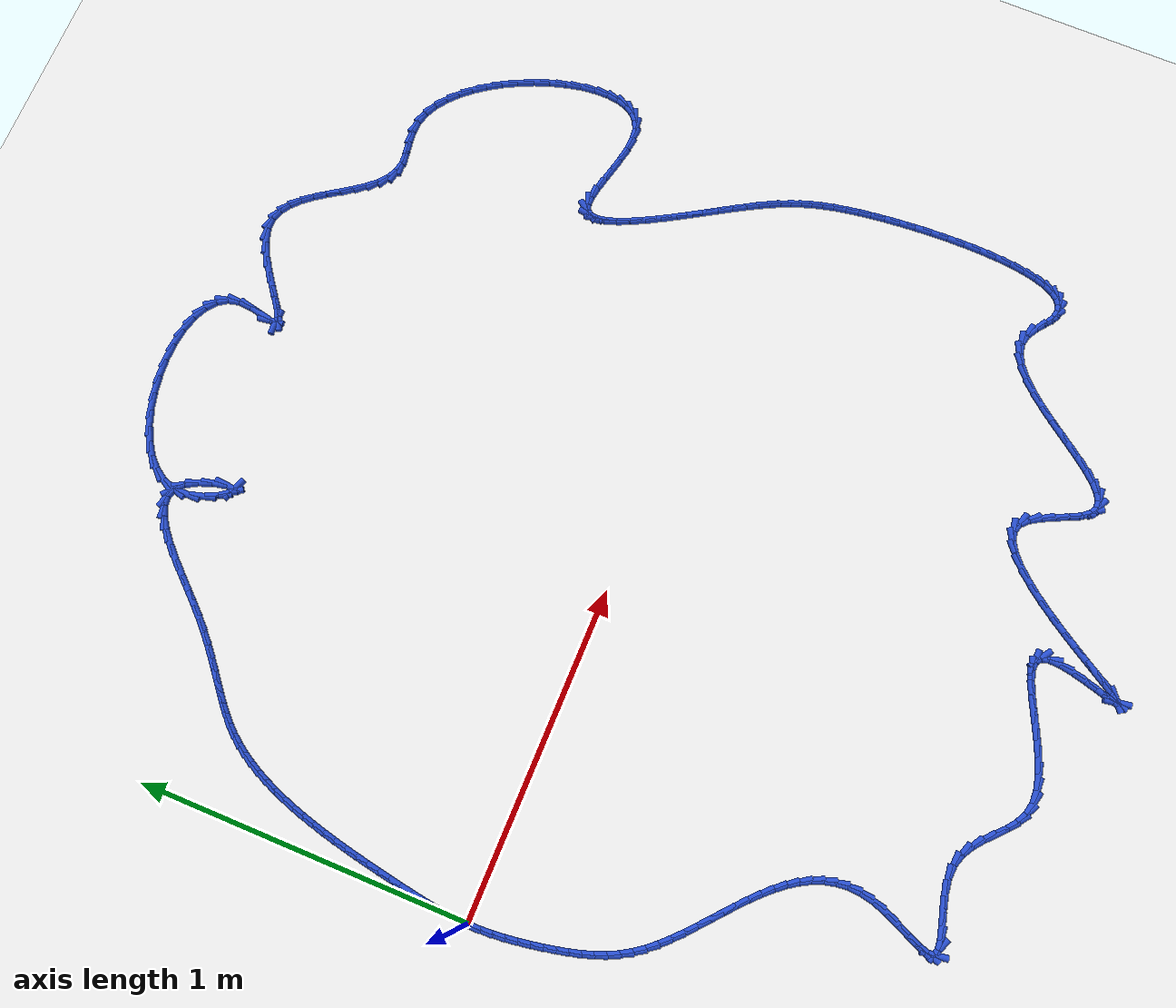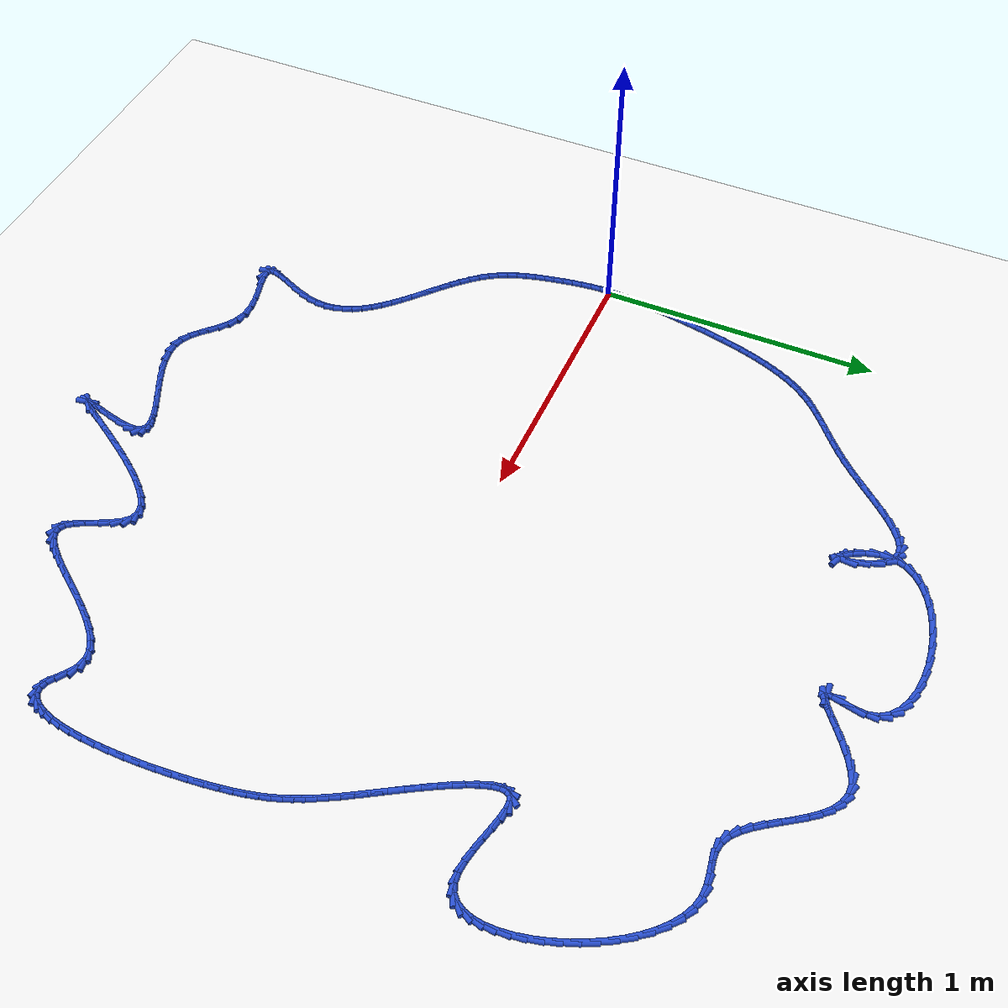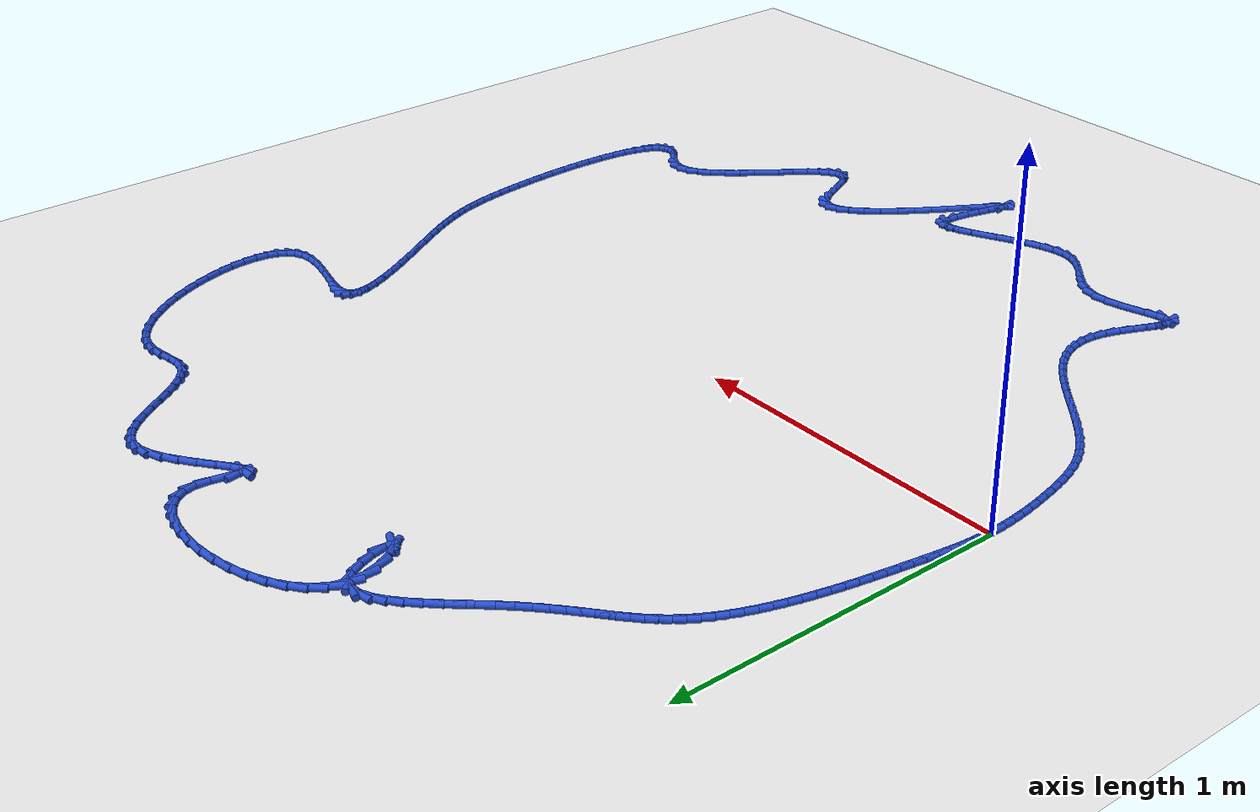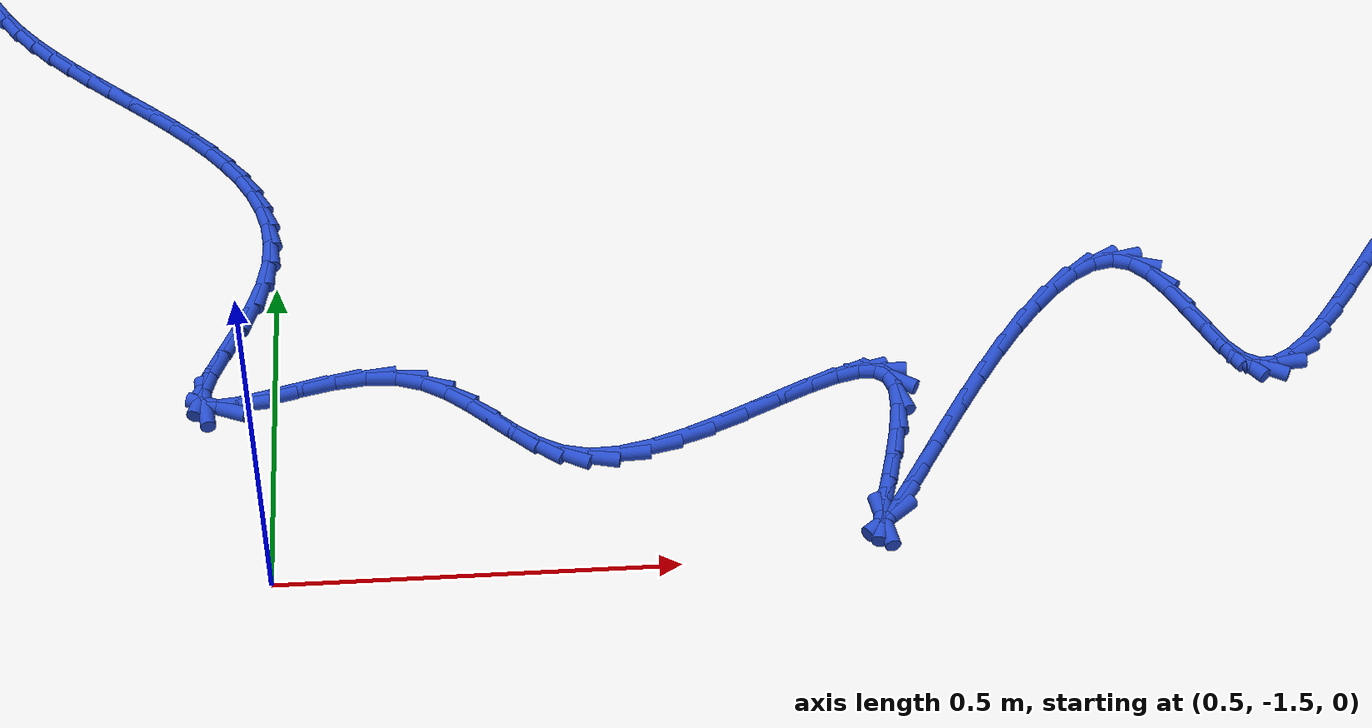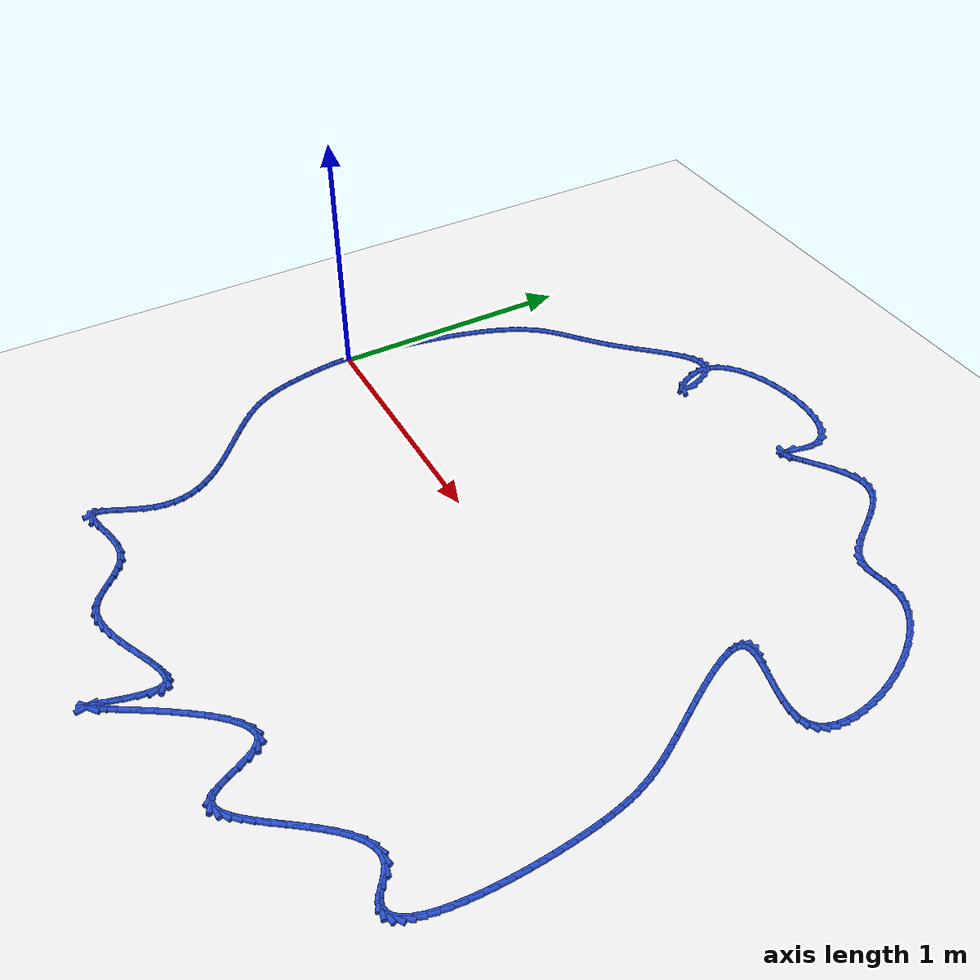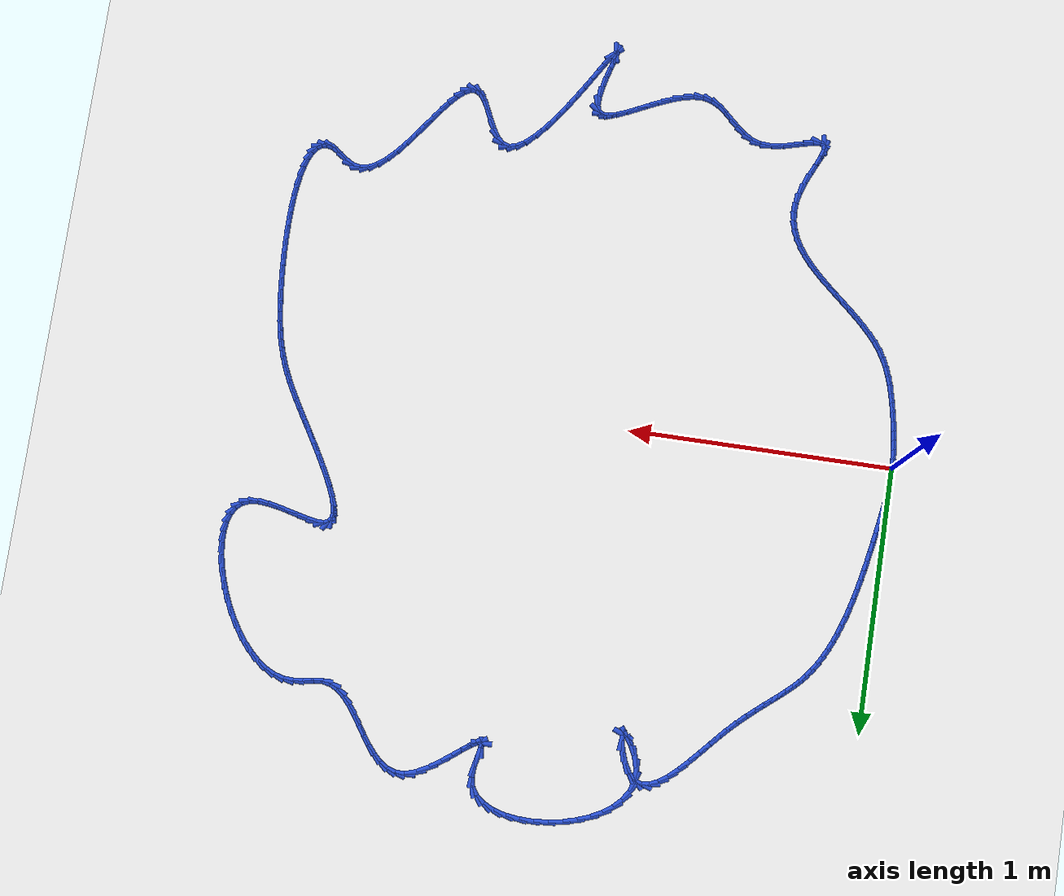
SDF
<sdf version="1.6">
 <world name="default">
  <light name="sun" type="directional">
   <pose>0 0 10 0 -0 0</pose>
   <diffuse>0.8 0.8 0.8 1</diffuse>
   <specular>0.2 0.2 0.2 1</specular>
   <attenuation>
    <range>1000</range>
    <constant>0.9</constant>
    <linear>0.01</linear>
    <quadratic>0.001</quadratic>
   </attenuation>
   <direction>-0.5 0.1 -0.9</direction>
  </light>
  <model name="ground_plane">
   <static>1</static>
   <link name="link">
    <collision name="collision">
     <geometry><plane><normal>0 0 1</normal><size>100 100</size></plane></geometry>
     <surface><friction><ode><mu>100</mu><mu2>50</mu2></ode></friction></surface>
    </collision>
    <visual name="visual">
     <cast_shadows>0</cast_shadows>
     <geometry><plane><normal>0 0 1</normal><size>100 100</size></plane></geometry>
     <material>
      <script><uri>file://media/materials/scripts/gazebo.material</uri><name>Gazebo/WhiteGlow</name></script>
     </material>
    </visual>
   </link>
  </model>
  <gravity>0 0 -9.8</gravity>
  <magnetic_field>6e-06 2.3e-05 -4.2e-05</magnetic_field>
  <atmosphere type="adiabatic"/>
  <physics name="default_physics" default="0" type="ode">
   <max_step_size>0.001</max_step_size>
   <real_time_factor>1</real_time_factor>
   <real_time_update_rate>1000</real_time_update_rate>
  </physics>
  <scene><ambient>0.4 0.4 0.4 1</ambient><background>0.7 0.7 0.7 1</background><shadows>1</shadows></scene>
  <spherical_coordinates>
   <surface_model>EARTH_WGS84</surface_model>
   <latitude_deg>0</latitude_deg>
   <longitude_deg>0</longitude_deg>
   <elevation>0</elevation>
   <heading_deg>0</heading_deg>
  </spherical_coordinates>
  <model name="line">
   <link name="link_0">
    <pose>8.673617379884035e-19 -6.938893903907228e-18 0.01 0 1.57 1.5414224761235265</pose>
    <collision name="collision">
     <geometry><cylinder><radius>0.01</radius><length>0.08</length></cylinder></geometry>
    </collision>
    <visual name="visual">
     <material>
      <script><name>Gazebo/Blue</name><uri>file://media/materials/scripts/gazebo.material</uri></script>
     </material>
     <geometry><cylinder><radius>0.01</radius><length>0.08</length></cylinder></geometry>
    </visual>
   </link>
   <link name="link_1">
    <pose>0.0010239473156294313 0.03484911852406405 0.01 0 1.57 1.499928040985235</pose>
    <collision name="collision">
     <geometry><cylinder><radius>0.01</radius><length>0.08</length></cylinder></geometry>
    </collision>
    <visual name="visual">
     <material>
      <script><name>Gazebo/Blue</name><uri>file://media/materials/scripts/gazebo.material</uri></script>
     </material>
     <geometry><cylinder><radius>0.01</radius><length>0.08</length></cylinder></geometry>
    </visual>
   </link>
   <link name="link_2">
    <pose>0.0034939503225837085 0.06964418305983518 0.01 0 1.57 1.4656953448621424</pose>
    <collision name="collision">
     <geometry><cylinder><radius>0.01</radius><length>0.08</length></cylinder></geometry>
    </collision>
    <visual name="visual">
     <material>
      <script><name>Gazebo/Blue</name><uri>file://media/materials/scripts/gazebo.material</uri></script>
     </material>
     <geometry><cylinder><radius>0.01</radius><length>0.08</length></cylinder></geometry>
    </visual>
   </link>
   <link name="link_3">
    <pose>0.007170091462013796 0.10449252868664313 0.01 0 1.57 1.4389605207833085</pose>
    <collision name="collision">
     <geometry><cylinder><radius>0.01</radius><length>0.08</length></cylinder></geometry>
    </collision>
    <visual name="visual">
     <material>
      <script><name>Gazebo/Blue</name><uri>file://media/materials/scripts/gazebo.material</uri></script>
     </material>
     <geometry><cylinder><radius>0.01</radius><length>0.08</length></cylinder></geometry>
    </visual>
   </link>
   <link name="link_4">
    <pose>0.011812453175070634 0.13950149048381752 0.01 0 1.57 1.4197688258746766</pose>
    <collision name="collision">
     <geometry><cylinder><radius>0.01</radius><length>0.08</length></cylinder></geometry>
    </collision>
    <visual name="visual">
     <material>
      <script><name>Gazebo/Blue</name><uri>file://media/materials/scripts/gazebo.material</uri></script>
     </material>
     <geometry><cylinder><radius>0.01</radius><length>0.08</length></cylinder></geometry>
    </visual>
   </link>
   <link name="link_5">
    <pose>0.0171811179029052 0.17477840353068816 0.01 0 1.57 1.4080224114338968</pose>
    <collision name="collision">
     <geometry><cylinder><radius>0.01</radius><length>0.08</length></cylinder></geometry>
    </collision>
    <visual name="visual">
     <material>
      <script><name>Gazebo/Blue</name><uri>file://media/materials/scripts/gazebo.material</uri></script>
     </material>
     <geometry><cylinder><radius>0.01</radius><length>0.08</length></cylinder></geometry>
    </visual>
   </link>
   <link name="link_6">
    <pose>0.023036168086668418 0.21043060290658455 0.01 0 1.57 1.4030618206520595</pose>
    <collision name="collision">
     <geometry><cylinder><radius>0.01</radius><length>0.08</length></cylinder></geometry>
    </collision>
    <visual name="visual">
     <material>
      <script><name>Gazebo/Blue</name><uri>file://media/materials/scripts/gazebo.material</uri></script>
     </material>
     <geometry><cylinder><radius>0.01</radius><length>0.08</length></cylinder></geometry>
    </visual>
   </link>
   <link name="link_7">
    <pose>0.02915269633009239 0.2465535088998982 0.01 0 1.57 1.3993205332500802</pose>
    <collision name="collision">
     <geometry><cylinder><radius>0.01</radius><length>0.08</length></cylinder></geometry>
    </collision>
    <visual name="visual">
     <material>
      <script><name>Gazebo/Blue</name><uri>file://media/materials/scripts/gazebo.material</uri></script>
     </material>
     <geometry><cylinder><radius>0.01</radius><length>0.08</length></cylinder></geometry>
    </visual>
   </link>
   <link name="link_8">
    <pose>0.035482133908054964 0.2831025674056935 0.01 0 1.57 1.3933005481091514</pose>
    <collision name="collision">
     <geometry><cylinder><radius>0.01</radius><length>0.08</length></cylinder></geometry>
    </collision>
    <visual name="visual">
     <material>
      <script><name>Gazebo/Blue</name><uri>file://media/materials/scripts/gazebo.material</uri></script>
     </material>
     <geometry><cylinder><radius>0.01</radius><length>0.08</length></cylinder></geometry>
    </visual>
   </link>
   <link name="link_9">
    <pose>0.04209056148565101 0.31994221774210724 0.01 0 1.57 1.384946077841931</pose>
    <collision name="collision">
     <geometry><cylinder><radius>0.01</radius><length>0.08</length></cylinder></geometry>
    </collision>
    <visual name="visual">
     <material>
      <script><name>Gazebo/Blue</name><uri>file://media/materials/scripts/gazebo.material</uri></script>
     </material>
     <geometry><cylinder><radius>0.01</radius><length>0.08</length></cylinder></geometry>
    </visual>
   </link>
   <link name="link_10">
    <pose>0.04904601059406098 0.35693535066566445 0.01 0 1.57 1.3742166747760323</pose>
    <collision name="collision">
     <geometry><cylinder><radius>0.01</radius><length>0.08</length></cylinder></geometry>
    </collision>
    <visual name="visual">
     <material>
      <script><name>Gazebo/Blue</name><uri>file://media/materials/scripts/gazebo.material</uri></script>
     </material>
     <geometry><cylinder><radius>0.01</radius><length>0.08</length></cylinder></geometry>
    </visual>
   </link>
   <link name="link_11">
    <pose>0.05641651276446533 0.39394485693289055 0.01 0 1.57 1.3610290885551308</pose>
    <collision name="collision">
     <geometry><cylinder><radius>0.01</radius><length>0.08</length></cylinder></geometry>
    </collision>
    <visual name="visual">
     <material>
      <script><name>Gazebo/Blue</name><uri>file://media/materials/scripts/gazebo.material</uri></script>
     </material>
     <geometry><cylinder><radius>0.01</radius><length>0.08</length></cylinder></geometry>
    </visual>
   </link>
   <link name="link_12">
    <pose>0.06427009952804444 0.4308336273003101 0.01 0 1.57 1.3452571864948786</pose>
    <collision name="collision">
     <geometry><cylinder><radius>0.01</radius><length>0.08</length></cylinder></geometry>
    </collision>
    <visual name="visual">
     <material>
      <script><name>Gazebo/Blue</name><uri>file://media/materials/scripts/gazebo.material</uri></script>
     </material>
     <geometry><cylinder><radius>0.01</radius><length>0.08</length></cylinder></geometry>
    </visual>
   </link>
   <link name="link_13">
    <pose>0.07267480241597878 0.46746455252444863 0.01 0 1.57 1.326730638230252</pose>
    <collision name="collision">
     <geometry><cylinder><radius>0.01</radius><length>0.08</length></cylinder></geometry>
    </collision>
    <visual name="visual">
     <material>
      <script><name>Gazebo/Blue</name><uri>file://media/materials/scripts/gazebo.material</uri></script>
     </material>
     <geometry><cylinder><radius>0.01</radius><length>0.08</length></cylinder></geometry>
    </visual>
   </link>
   <link name="link_14">
    <pose>0.08169865295944875 0.5037005233618311 0.01 0 1.57 1.305232618522365</pose>
    <collision name="collision">
     <geometry><cylinder><radius>0.01</radius><length>0.08</length></cylinder></geometry>
    </collision>
    <visual name="visual">
     <material>
      <script><name>Gazebo/Blue</name><uri>file://media/materials/scripts/gazebo.material</uri></script>
     </material>
     <geometry><cylinder><radius>0.01</radius><length>0.08</length></cylinder></geometry>
    </visual>
   </link>
   <link name="link_15">
    <pose>0.09140968268963484 0.5394044305689827 0.01 0 1.57 1.280496841751614</pose>
    <collision name="collision">
     <geometry><cylinder><radius>0.01</radius><length>0.08</length></cylinder></geometry>
    </collision>
    <visual name="visual">
     <material>
      <script><name>Gazebo/Blue</name><uri>file://media/materials/scripts/gazebo.material</uri></script>
     </material>
     <geometry><cylinder><radius>0.01</radius><length>0.08</length></cylinder></geometry>
    </visual>
   </link>
   <link name="link_16">
    <pose>0.10187592313771746 0.5744391649024285 0.01 0 1.57 1.2522043899458992</pose>
    <collision name="collision">
     <geometry><cylinder><radius>0.01</radius><length>0.08</length></cylinder></geometry>
    </collision>
    <visual name="visual">
     <material>
      <script><name>Gazebo/Blue</name><uri>file://media/materials/scripts/gazebo.material</uri></script>
     </material>
     <geometry><cylinder><radius>0.01</radius><length>0.08</length></cylinder></geometry>
    </visual>
   </link>
   <link name="link_17">
    <pose>0.11316540583487703 0.6086676171186937 0.01 0 1.57 1.2199810689688901</pose>
    <collision name="collision">
     <geometry><cylinder><radius>0.01</radius><length>0.08</length></cylinder></geometry>
    </collision>
    <visual name="visual">
     <material>
      <script><name>Gazebo/Blue</name><uri>file://media/materials/scripts/gazebo.material</uri></script>
     </material>
     <geometry><cylinder><radius>0.01</radius><length>0.08</length></cylinder></geometry>
    </visual>
   </link>
   <link name="link_18">
    <pose>0.12534616231229395 0.6419526779743031 0.01 0 1.57 1.1833964749011565</pose>
    <collision name="collision">
     <geometry><cylinder><radius>0.01</radius><length>0.08</length></cylinder></geometry>
    </collision>
    <visual name="visual">
     <material>
      <script><name>Gazebo/Blue</name><uri>file://media/materials/scripts/gazebo.material</uri></script>
     </material>
     <geometry><cylinder><radius>0.01</radius><length>0.08</length></cylinder></geometry>
    </visual>
   </link>
   <link name="link_19">
    <pose>0.13848622410114875 0.6741572382257821 0.01 0 1.57 1.1419666333014822</pose>
    <collision name="collision">
     <geometry><cylinder><radius>0.01</radius><length>0.08</length></cylinder></geometry>
    </collision>
    <visual name="visual">
     <material>
      <script><name>Gazebo/Blue</name><uri>file://media/materials/scripts/gazebo.material</uri></script>
     </material>
     <geometry><cylinder><radius>0.01</radius><length>0.08</length></cylinder></geometry>
    </visual>
   </link>
   <link name="link_20">
    <pose>0.15265362273262179 0.7051441886296558 0.01 0 1.57 1.0951630324885584</pose>
    <collision name="collision">
     <geometry><cylinder><radius>0.01</radius><length>0.08</length></cylinder></geometry>
    </collision>
    <visual name="visual">
     <material>
      <script><name>Gazebo/Blue</name><uri>file://media/materials/scripts/gazebo.material</uri></script>
     </material>
     <geometry><cylinder><radius>0.01</radius><length>0.08</length></cylinder></geometry>
    </visual>
   </link>
   <link name="link_21">
    <pose>0.16791638973789355 0.7347764199424494 0.01 0 1.57 1.0424320808337457</pose>
    <collision name="collision">
     <geometry><cylinder><radius>0.01</radius><length>0.08</length></cylinder></geometry>
    </collision>
    <visual name="visual">
     <material>
      <script><name>Gazebo/Blue</name><uri>file://media/materials/scripts/gazebo.material</uri></script>
     </material>
     <geometry><cylinder><radius>0.01</radius><length>0.08</length></cylinder></geometry>
    </visual>
   </link>
   <link name="link_22">
    <pose>0.18434255664814442 0.7629168229206876 0.01 0 1.57 0.983230257297972</pose>
    <collision name="collision">
     <geometry><cylinder><radius>0.01</radius><length>0.08</length></cylinder></geometry>
    </collision>
    <visual name="visual">
     <material>
      <script><name>Gazebo/Blue</name><uri>file://media/materials/scripts/gazebo.material</uri></script>
     </material>
     <geometry><cylinder><radius>0.01</radius><length>0.08</length></cylinder></geometry>
    </visual>
   </link>
   <link name="link_23">
    <pose>0.20200015499455493 0.789428288320896 0.01 0 1.57 0.9170908954530885</pose>
    <collision name="collision">
     <geometry><cylinder><radius>0.01</radius><length>0.08</length></cylinder></geometry>
    </collision>
    <visual name="visual">
     <material>
      <script><name>Gazebo/Blue</name><uri>file://media/materials/scripts/gazebo.material</uri></script>
     </material>
     <geometry><cylinder><radius>0.01</radius><length>0.08</length></cylinder></geometry>
    </visual>
   </link>
   <link name="link_24">
    <pose>0.2209571533859981 0.8141741382692911 0.01 0 1.57 0.8479554641206369</pose>
    <collision name="collision">
     <geometry><cylinder><radius>0.01</radius><length>0.08</length></cylinder></geometry>
    </collision>
    <visual name="visual">
     <material>
      <script><name>Gazebo/Blue</name><uri>file://media/materials/scripts/gazebo.material</uri></script>
     </material>
     <geometry><cylinder><radius>0.01</radius><length>0.08</length></cylinder></geometry>
    </visual>
   </link>
   <link name="link_25">
    <pose>0.24125684260298844 0.8371868760248691 0.01 0 1.57 0.7880293055103469</pose>
    <collision name="collision">
     <geometry><cylinder><radius>0.01</radius><length>0.08</length></cylinder></geometry>
    </collision>
    <visual name="visual">
     <material>
      <script><name>Gazebo/Blue</name><uri>file://media/materials/scripts/gazebo.material</uri></script>
     </material>
     <geometry><cylinder><radius>0.01</radius><length>0.08</length></cylinder></geometry>
    </visual>
   </link>
   <link name="link_26">
    <pose>0.26288043892727603 0.8589245623091757 0.01 0 1.57 0.7414103494423929</pose>
    <collision name="collision">
     <geometry><cylinder><radius>0.01</radius><length>0.08</length></cylinder></geometry>
    </collision>
    <visual name="visual">
     <material>
      <script><name>Gazebo/Blue</name><uri>file://media/materials/scripts/gazebo.material</uri></script>
     </material>
     <geometry><cylinder><radius>0.01</radius><length>0.08</length></cylinder></geometry>
    </visual>
   </link>
   <link name="link_27">
    <pose>0.28579955232514975 0.8799111148271134 0.01 0 1.57 0.7092997654228262</pose>
    <collision name="collision">
     <geometry><cylinder><radius>0.01</radius><length>0.08</length></cylinder></geometry>
    </collision>
    <visual name="visual">
     <material>
      <script><name>Gazebo/Blue</name><uri>file://media/materials/scripts/gazebo.material</uri></script>
     </material>
     <geometry><cylinder><radius>0.01</radius><length>0.08</length></cylinder></geometry>
    </visual>
   </link>
   <link name="link_28">
    <pose>0.30998579276289895 0.9006704512835848 0.01 0 1.57 0.6916794545246121</pose>
    <collision name="collision">
     <geometry><cylinder><radius>0.01</radius><length>0.08</length></cylinder></geometry>
    </collision>
    <visual name="visual">
     <material>
      <script><name>Gazebo/Blue</name><uri>file://media/materials/scripts/gazebo.material</uri></script>
     </material>
     <geometry><cylinder><radius>0.01</radius><length>0.08</length></cylinder></geometry>
    </visual>
   </link>
   <link name="link_29">
    <pose>0.3354107702068125 0.9217264893834933 0.01 0 1.57 0.6876183692868023</pose>
    <collision name="collision">
     <geometry><cylinder><radius>0.01</radius><length>0.08</length></cylinder></geometry>
    </collision>
    <visual name="visual">
     <material>
      <script><name>Gazebo/Blue</name><uri>file://media/materials/scripts/gazebo.material</uri></script>
     </material>
     <geometry><cylinder><radius>0.01</radius><length>0.08</length></cylinder></geometry>
    </visual>
   </link>
   <link name="link_30">
    <pose>0.3620460946231796 0.9436031468317415 0.01 0 1.57 0.6955889898252542</pose>
    <collision name="collision">
     <geometry><cylinder><radius>0.01</radius><length>0.08</length></cylinder></geometry>
    </collision>
    <visual name="visual">
     <material>
      <script><name>Gazebo/Blue</name><uri>file://media/materials/scripts/gazebo.material</uri></script>
     </material>
     <geometry><cylinder><radius>0.01</radius><length>0.08</length></cylinder></geometry>
    </visual>
   </link>
   <link name="link_31">
    <pose>0.38986337597828924 0.9668243413332324 0.01 0 1.57 0.7137275091206661</pose>
    <collision name="collision">
     <geometry><cylinder><radius>0.01</radius><length>0.08</length></cylinder></geometry>
    </collision>
    <visual name="visual">
     <material>
      <script><name>Gazebo/Blue</name><uri>file://media/materials/scripts/gazebo.material</uri></script>
     </material>
     <geometry><cylinder><radius>0.01</radius><length>0.08</length></cylinder></geometry>
    </visual>
   </link>
   <link name="link_32">
    <pose>0.41883422423843053 0.9919139905928684 0.01 0 1.57 0.7400300089661886</pose>
    <collision name="collision">
     <geometry><cylinder><radius>0.01</radius><length>0.08</length></cylinder></geometry>
    </collision>
    <visual name="visual">
     <material>
      <script><name>Gazebo/Blue</name><uri>file://media/materials/scripts/gazebo.material</uri></script>
     </material>
     <geometry><cylinder><radius>0.01</radius><length>0.08</length></cylinder></geometry>
    </visual>
   </link>
   <link name="link_33">
    <pose>0.4489302493698926 1.019396012315553 0.01 0 1.57 0.7724992915316626</pose>
    <collision name="collision">
     <geometry><cylinder><radius>0.01</radius><length>0.08</length></cylinder></geometry>
    </collision>
    <visual name="visual">
     <material>
      <script><name>Gazebo/Blue</name><uri>file://media/materials/scripts/gazebo.material</uri></script>
     </material>
     <geometry><cylinder><radius>0.01</radius><length>0.08</length></cylinder></geometry>
    </visual>
   </link>
   <link name="link_34">
    <pose>0.48012306133896443 1.0497943242061885 0.01 0 1.57 0.8080976363440308</pose>
    <collision name="collision">
     <geometry><cylinder><radius>0.01</radius><length>0.08</length></cylinder></geometry>
    </collision>
    <visual name="visual">
     <material>
      <script><name>Gazebo/Blue</name><uri>file://media/materials/scripts/gazebo.material</uri></script>
     </material>
     <geometry><cylinder><radius>0.01</radius><length>0.08</length></cylinder></geometry>
    </visual>
   </link>
   <link name="link_35">
    <pose>0.5123705516127621 1.0835400838149782 0.01 0 1.57 0.8311679696498147</pose>
    <collision name="collision">
     <geometry><cylinder><radius>0.01</radius><length>0.08</length></cylinder></geometry>
    </collision>
    <visual name="visual">
     <material>
      <script><name>Gazebo/Blue</name><uri>file://media/materials/scripts/gazebo.material</uri></script>
     </material>
     <geometry><cylinder><radius>0.01</radius><length>0.08</length></cylinder></geometry>
    </visual>
   </link>
   <link name="link_36">
    <pose>0.5454415224517037 1.1197858872515476 0.01 0 1.57 0.8341838294463393</pose>
    <collision name="collision">
     <geometry><cylinder><radius>0.01</radius><length>0.08</length></cylinder></geometry>
    </collision>
    <visual name="visual">
     <material>
      <script><name>Gazebo/Blue</name><uri>file://media/materials/scripts/gazebo.material</uri></script>
     </material>
     <geometry><cylinder><radius>0.01</radius><length>0.08</length></cylinder></geometry>
    </visual>
   </link>
   <link name="link_37">
    <pose>0.578967070326665 1.1567532076083569 0.01 0 1.57 0.8182096686960248</pose>
    <collision name="collision">
     <geometry><cylinder><radius>0.01</radius><length>0.08</length></cylinder></geometry>
    </collision>
    <visual name="visual">
     <material>
      <script><name>Gazebo/Blue</name><uri>file://media/materials/scripts/gazebo.material</uri></script>
     </material>
     <geometry><cylinder><radius>0.01</radius><length>0.08</length></cylinder></geometry>
    </visual>
   </link>
   <link name="link_38">
    <pose>0.6125751749175075 1.1926424432223204 0.01 0 1.57 0.780768452800222</pose>
    <collision name="collision">
     <geometry><cylinder><radius>0.01</radius><length>0.08</length></cylinder></geometry>
    </collision>
    <visual name="visual">
     <material>
      <script><name>Gazebo/Blue</name><uri>file://media/materials/scripts/gazebo.material</uri></script>
     </material>
     <geometry><cylinder><radius>0.01</radius><length>0.08</length></cylinder></geometry>
    </visual>
   </link>
   <link name="link_39">
    <pose>0.6458938159040948 1.2256539924303536 0.01 0 1.57 0.7146393745853895</pose>
    <collision name="collision">
     <geometry><cylinder><radius>0.01</radius><length>0.08</length></cylinder></geometry>
    </collision>
    <visual name="visual">
     <material>
      <script><name>Gazebo/Blue</name><uri>file://media/materials/scripts/gazebo.material</uri></script>
     </material>
     <geometry><cylinder><radius>0.01</radius><length>0.08</length></cylinder></geometry>
    </visual>
   </link>
   <link name="link_40">
    <pose>0.6785509729662886 1.2539882535693712 0.01 0 1.57 0.6047762715896927</pose>
    <collision name="collision">
     <geometry><cylinder><radius>0.01</radius><length>0.08</length></cylinder></geometry>
    </collision>
    <visual name="visual">
     <material>
      <script><name>Gazebo/Blue</name><uri>file://media/materials/scripts/gazebo.material</uri></script>
     </material>
     <geometry><cylinder><radius>0.01</radius><length>0.08</length></cylinder></geometry>
    </visual>
   </link>
   <link name="link_41">
    <pose>0.7101746257839522 1.2758456249762888 0.01 0 1.57 0.4223783432243723</pose>
    <collision name="collision">
     <geometry><cylinder><radius>0.01</radius><length>0.08</length></cylinder></geometry>
    </collision>
    <visual name="visual">
     <material>
      <script><name>Gazebo/Blue</name><uri>file://media/materials/scripts/gazebo.material</uri></script>
     </material>
     <geometry><cylinder><radius>0.01</radius><length>0.08</length></cylinder></geometry>
    </visual>
   </link>
   <link name="link_42">
    <pose>0.740392754036947 1.2894265049880203 0.01 0 1.57 0.12261371296069828</pose>
    <collision name="collision">
     <geometry><cylinder><radius>0.01</radius><length>0.08</length></cylinder></geometry>
    </collision>
    <visual name="visual">
     <material>
      <script><name>Gazebo/Blue</name><uri>file://media/materials/scripts/gazebo.material</uri></script>
     </material>
     <geometry><cylinder><radius>0.01</radius><length>0.08</length></cylinder></geometry>
    </visual>
   </link>
   <link name="link_43">
    <pose>0.7688333374051366 1.2929312919414815 0.01 0 1.57 -0.3082456287313501</pose>
    <collision name="collision">
     <geometry><cylinder><radius>0.01</radius><length>0.08</length></cylinder></geometry>
    </collision>
    <visual name="visual">
     <material>
      <script><name>Gazebo/Blue</name><uri>file://media/materials/scripts/gazebo.material</uri></script>
     </material>
     <geometry><cylinder><radius>0.01</radius><length>0.08</length></cylinder></geometry>
    </visual>
   </link>
   <link name="link_44">
    <pose>0.7951243555683829 1.284560384173587 0.01 0 1.57 -0.74780365004351</pose>
    <collision name="collision">
     <geometry><cylinder><radius>0.01</radius><length>0.08</length></cylinder></geometry>
    </collision>
    <visual name="visual">
     <material>
      <script><name>Gazebo/Blue</name><uri>file://media/materials/scripts/gazebo.material</uri></script>
     </material>
     <geometry><cylinder><radius>0.01</radius><length>0.08</length></cylinder></geometry>
    </visual>
   </link>
   <link name="link_45">
    <pose>0.8188937882065485 1.262514180021252 0.01 0 1.57 -1.0548621084331538</pose>
    <collision name="collision">
     <geometry><cylinder><radius>0.01</radius><length>0.08</length></cylinder></geometry>
    </collision>
    <visual name="visual">
     <material>
      <script><name>Gazebo/Blue</name><uri>file://media/materials/scripts/gazebo.material</uri></script>
     </material>
     <geometry><cylinder><radius>0.01</radius><length>0.08</length></cylinder></geometry>
    </visual>
   </link>
   <link name="link_46">
    <pose>0.8396079270320379 1.2259926234696037 0.01 0 1.57 -1.2220957559005912</pose>
    <collision name="collision">
     <geometry><cylinder><radius>0.01</radius><length>0.08</length></cylinder></geometry>
    </collision>
    <visual name="visual">
     <material>
      <script><name>Gazebo/Blue</name><uri>file://media/materials/scripts/gazebo.material</uri></script>
     </material>
     <geometry><cylinder><radius>0.01</radius><length>0.08</length></cylinder></geometry>
    </visual>
   </link>
   <link name="link_47">
    <pose>0.8553655190994893 1.1826497403559655 0.01 0 1.57 -1.3593594995580638</pose>
    <collision name="collision">
     <geometry><cylinder><radius>0.01</radius><length>0.08</length></cylinder></geometry>
    </collision>
    <visual name="visual">
     <material>
      <script><name>Gazebo/Blue</name><uri>file://media/materials/scripts/gazebo.material</uri></script>
     </material>
     <geometry><cylinder><radius>0.01</radius><length>0.08</length></cylinder></geometry>
    </visual>
   </link>
   <link name="link_48">
    <pose>0.8635776683142906 1.1443905266310386 0.01 0 1.57 1.4802933757255572</pose>
    <collision name="collision">
     <geometry><cylinder><radius>0.01</radius><length>0.08</length></cylinder></geometry>
    </collision>
    <visual name="visual">
     <material>
      <script><name>Gazebo/Blue</name><uri>file://media/materials/scripts/gazebo.material</uri></script>
     </material>
     <geometry><cylinder><radius>0.01</radius><length>0.08</length></cylinder></geometry>
    </visual>
   </link>
   <link name="link_49">
    <pose>0.8616502699073799 1.123152177969227 0.01 0 1.57 -0.38003708982980605</pose>
    <collision name="collision">
     <geometry><cylinder><radius>0.01</radius><length>0.08</length></cylinder></geometry>
    </collision>
    <visual name="visual">
     <material>
      <script><name>Gazebo/Blue</name><uri>file://media/materials/scripts/gazebo.material</uri></script>
     </material>
     <geometry><cylinder><radius>0.01</radius><length>0.08</length></cylinder></geometry>
    </visual>
   </link>
   <link name="link_50">
    <pose>0.8480536195474618 1.1285834378490758 0.01 0 1.57 -0.9412311982583728</pose>
    <collision name="collision">
     <geometry><cylinder><radius>0.01</radius><length>0.08</length></cylinder></geometry>
    </collision>
    <visual name="visual">
     <material>
      <script><name>Gazebo/Blue</name><uri>file://media/materials/scripts/gazebo.material</uri></script>
     </material>
     <geometry><cylinder><radius>0.01</radius><length>0.08</length></cylinder></geometry>
    </visual>
   </link>
   <link name="link_51">
    <pose>0.8276464142431103 1.156598039356859 0.01 0 1.57 -1.1211320933706357</pose>
    <collision name="collision">
     <geometry><cylinder><radius>0.01</radius><length>0.08</length></cylinder></geometry>
    </collision>
    <visual name="visual">
     <material>
      <script><name>Gazebo/Blue</name><uri>file://media/materials/scripts/gazebo.material</uri></script>
     </material>
     <geometry><cylinder><radius>0.01</radius><length>0.08</length></cylinder></geometry>
    </visual>
   </link>
   <link name="link_52">
    <pose>0.8076597823152123 1.1980090077497736 0.01 0 1.57 -1.3066910710389916</pose>
    <collision name="collision">
     <geometry><cylinder><radius>0.01</radius><length>0.08</length></cylinder></geometry>
    </collision>
    <visual name="visual">
     <material>
      <script><name>Gazebo/Blue</name><uri>file://media/materials/scripts/gazebo.material</uri></script>
     </material>
     <geometry><cylinder><radius>0.01</radius><length>0.08</length></cylinder></geometry>
    </visual>
   </link>
   <link name="link_53">
    <pose>0.795323969610544 1.2436258807061757 0.01 0 1.57 1.5627005516731884</pose>
    <collision name="collision">
     <geometry><cylinder><radius>0.01</radius><length>0.08</length></cylinder></geometry>
    </collision>
    <visual name="visual">
     <material>
      <script><name>Gazebo/Blue</name><uri>file://media/materials/scripts/gazebo.material</uri></script>
     </material>
     <geometry><cylinder><radius>0.01</radius><length>0.08</length></cylinder></geometry>
    </visual>
   </link>
   <link name="link_54">
    <pose>0.7956712769642732 1.2865247706561351 0.01 0 1.57 1.2639186267338465</pose>
    <collision name="collision">
     <geometry><cylinder><radius>0.01</radius><length>0.08</length></cylinder></geometry>
    </collision>
    <visual name="visual">
     <material>
      <script><name>Gazebo/Blue</name><uri>file://media/materials/scripts/gazebo.material</uri></script>
     </material>
     <geometry><cylinder><radius>0.01</radius><length>0.08</length></cylinder></geometry>
    </visual>
   </link>
   <link name="link_55">
    <pose>0.8080631684792999 1.3256296958192586 0.01 0 1.57 0.9936578278577751</pose>
    <collision name="collision">
     <geometry><cylinder><radius>0.01</radius><length>0.08</length></cylinder></geometry>
    </collision>
    <visual name="visual">
     <material>
      <script><name>Gazebo/Blue</name><uri>file://media/materials/scripts/gazebo.material</uri></script>
     </material>
     <geometry><cylinder><radius>0.01</radius><length>0.08</length></cylinder></geometry>
    </visual>
   </link>
   <link name="link_56">
    <pose>0.8309588708674229 1.3607950837201697 0.01 0 1.57 0.7730302850920502</pose>
    <collision name="collision">
     <geometry><cylinder><radius>0.01</radius><length>0.08</length></cylinder></geometry>
    </collision>
    <visual name="visual">
     <material>
      <script><name>Gazebo/Blue</name><uri>file://media/materials/scripts/gazebo.material</uri></script>
     </material>
     <geometry><cylinder><radius>0.01</radius><length>0.08</length></cylinder></geometry>
    </visual>
   </link>
   <link name="link_57">
    <pose>0.8628176108404417 1.391875361883494 0.01 0 1.57 0.5995839545442522</pose>
    <collision name="collision">
     <geometry><cylinder><radius>0.01</radius><length>0.08</length></cylinder></geometry>
    </collision>
    <visual name="visual">
     <material>
      <script><name>Gazebo/Blue</name><uri>file://media/materials/scripts/gazebo.material</uri></script>
     </material>
     <geometry><cylinder><radius>0.01</radius><length>0.08</length></cylinder></geometry>
    </visual>
   </link>
   <link name="link_58">
    <pose>0.9020986151101548 1.4187249578338554 0.01 0 1.57 0.4617343494042436</pose>
    <collision name="collision">
     <geometry><cylinder><radius>0.01</radius><length>0.08</length></cylinder></geometry>
    </collision>
    <visual name="visual">
     <material>
      <script><name>Gazebo/Blue</name><uri>file://media/materials/scripts/gazebo.material</uri></script>
     </material>
     <geometry><cylinder><radius>0.01</radius><length>0.08</length></cylinder></geometry>
    </visual>
   </link>
   <link name="link_59">
    <pose>0.9472611103883621 1.4411982990958792 0.01 0 1.57 0.3478848116614605</pose>
    <collision name="collision">
     <geometry><cylinder><radius>0.01</radius><length>0.08</length></cylinder></geometry>
    </collision>
    <visual name="visual">
     <material>
      <script><name>Gazebo/Blue</name><uri>file://media/materials/scripts/gazebo.material</uri></script>
     </material>
     <geometry><cylinder><radius>0.01</radius><length>0.08</length></cylinder></geometry>
    </visual>
   </link>
   <link name="link_60">
    <pose>0.9967643233868619 1.45914981319419 0.01 0 1.57 0.24872387078479347</pose>
    <collision name="collision">
     <geometry><cylinder><radius>0.01</radius><length>0.08</length></cylinder></geometry>
    </collision>
    <visual name="visual">
     <material>
      <script><name>Gazebo/Blue</name><uri>file://media/materials/scripts/gazebo.material</uri></script>
     </material>
     <geometry><cylinder><radius>0.01</radius><length>0.08</length></cylinder></geometry>
    </visual>
   </link>
   <link name="link_61">
    <pose>1.0490674808174545 1.472433927653412 0.01 0 1.57 0.15685565841486598</pose>
    <collision name="collision">
     <geometry><cylinder><radius>0.01</radius><length>0.08</length></cylinder></geometry>
    </collision>
    <visual name="visual">
     <material>
      <script><name>Gazebo/Blue</name><uri>file://media/materials/scripts/gazebo.material</uri></script>
     </material>
     <geometry><cylinder><radius>0.01</radius><length>0.08</length></cylinder></geometry>
    </visual>
   </link>
   <link name="link_62">
    <pose>1.102629809391938 1.4809050699981707 0.01 0 1.57 0.06583097344384599</pose>
    <collision name="collision">
     <geometry><cylinder><radius>0.01</radius><length>0.08</length></cylinder></geometry>
    </collision>
    <visual name="visual">
     <material>
      <script><name>Gazebo/Blue</name><uri>file://media/materials/scripts/gazebo.material</uri></script>
     </material>
     <geometry><cylinder><radius>0.01</radius><length>0.08</length></cylinder></geometry>
    </visual>
   </link>
   <link name="link_63">
    <pose>1.1559105358221127 1.4844176677530905 0.01 0 1.57 -0.030918443933877677</pose>
    <collision name="collision">
     <geometry><cylinder><radius>0.01</radius><length>0.08</length></cylinder></geometry>
    </collision>
    <visual name="visual">
     <material>
      <script><name>Gazebo/Blue</name><uri>file://media/materials/scripts/gazebo.material</uri></script>
     </material>
     <geometry><cylinder><radius>0.01</radius><length>0.08</length></cylinder></geometry>
    </visual>
   </link>
   <link name="link_64">
    <pose>1.207368886819776 1.4828261484427954 0.01 0 1.57 -0.14129520392929415</pose>
    <collision name="collision">
     <geometry><cylinder><radius>0.01</radius><length>0.08</length></cylinder></geometry>
    </collision>
    <visual name="visual">
     <material>
      <script><name>Gazebo/Blue</name><uri>file://media/materials/scripts/gazebo.material</uri></script>
     </material>
     <geometry><cylinder><radius>0.01</radius><length>0.08</length></cylinder></geometry>
    </visual>
   </link>
   <link name="link_65">
    <pose>1.2554640890967288 1.4759849395919113 0.01 0 1.57 -0.2760743322663576</pose>
    <collision name="collision">
     <geometry><cylinder><radius>0.01</radius><length>0.08</length></cylinder></geometry>
    </collision>
    <visual name="visual">
     <material>
      <script><name>Gazebo/Blue</name><uri>file://media/materials/scripts/gazebo.material</uri></script>
     </material>
     <geometry><cylinder><radius>0.01</radius><length>0.08</length></cylinder></geometry>
    </visual>
   </link>
   <link name="link_66">
    <pose>1.2986553693647696 1.4637484687250621 0.01 0 1.57 -0.45058855030204903</pose>
    <collision name="collision">
     <geometry><cylinder><radius>0.01</radius><length>0.08</length></cylinder></geometry>
    </collision>
    <visual name="visual">
     <material>
      <script><name>Gazebo/Blue</name><uri>file://media/materials/scripts/gazebo.material</uri></script>
     </material>
     <geometry><cylinder><radius>0.01</radius><length>0.08</length></cylinder></geometry>
    </visual>
   </link>
   <link name="link_67">
    <pose>1.3354019543356972 1.4459711633668726 0.01 0 1.57 -0.6843093279620954</pose>
    <collision name="collision">
     <geometry><cylinder><radius>0.01</radius><length>0.08</length></cylinder></geometry>
    </collision>
    <visual name="visual">
     <material>
      <script><name>Gazebo/Blue</name><uri>file://media/materials/scripts/gazebo.material</uri></script>
     </material>
     <geometry><cylinder><radius>0.01</radius><length>0.08</length></cylinder></geometry>
    </visual>
   </link>
   <link name="link_68">
    <pose>1.3641630707213115 1.4225074510419677 0.01 0 1.57 -0.989811511522134</pose>
    <collision name="collision">
     <geometry><cylinder><radius>0.01</radius><length>0.08</length></cylinder></geometry>
    </collision>
    <visual name="visual">
     <material>
      <script><name>Gazebo/Blue</name><uri>file://media/materials/scripts/gazebo.material</uri></script>
     </material>
     <geometry><cylinder><radius>0.01</radius><length>0.08</length></cylinder></geometry>
    </visual>
   </link>
   <link name="link_69">
    <pose>1.3833979452334115 1.3932117592749724 0.01 0 1.57 -1.3432471710661074</pose>
    <collision name="collision">
     <geometry><cylinder><radius>0.01</radius><length>0.08</length></cylinder></geometry>
    </collision>
    <visual name="visual">
     <material>
      <script><name>Gazebo/Blue</name><uri>file://media/materials/scripts/gazebo.material</uri></script>
     </material>
     <geometry><cylinder><radius>0.01</radius><length>0.08</length></cylinder></geometry>
    </visual>
   </link>
   <link name="link_70">
    <pose>1.3915658045837955 1.3579385155905102 0.01 0 1.57 1.4942122126148025</pose>
    <collision name="collision">
     <geometry><cylinder><radius>0.01</radius><length>0.08</length></cylinder></geometry>
    </collision>
    <visual name="visual">
     <material>
      <script><name>Gazebo/Blue</name><uri>file://media/materials/scripts/gazebo.material</uri></script>
     </material>
     <geometry><cylinder><radius>0.01</radius><length>0.08</length></cylinder></geometry>
    </visual>
   </link>
   <link name="link_71">
    <pose>1.3884750019547014 1.3176591750437523 0.01 0 1.57 1.3556691968439516</pose>
    <collision name="collision">
     <geometry><cylinder><radius>0.01</radius><length>0.08</length></cylinder></geometry>
    </collision>
    <visual name="visual">
     <material>
      <script><name>Gazebo/Blue</name><uri>file://media/materials/scripts/gazebo.material</uri></script>
     </material>
     <geometry><cylinder><radius>0.01</radius><length>0.08</length></cylinder></geometry>
    </visual>
   </link>
   <link name="link_72">
    <pose>1.3798650765142189 1.278255998444669 0.01 0 1.57 1.358058329380303</pose>
    <collision name="collision">
     <geometry><cylinder><radius>0.01</radius><length>0.08</length></cylinder></geometry>
    </collision>
    <visual name="visual">
     <material>
      <script><name>Gazebo/Blue</name><uri>file://media/materials/scripts/gazebo.material</uri></script>
     </material>
     <geometry><cylinder><radius>0.01</radius><length>0.08</length></cylinder></geometry>
    </visual>
   </link>
   <link name="link_73">
    <pose>1.3731050175448636 1.2469603718908497 0.01 0 1.57 -1.4364821296150232</pose>
    <collision name="collision">
     <geometry><cylinder><radius>0.01</radius><length>0.08</length></cylinder></geometry>
    </collision>
    <visual name="visual">
     <material>
      <script><name>Gazebo/Blue</name><uri>file://media/materials/scripts/gazebo.material</uri></script>
     </material>
     <geometry><cylinder><radius>0.01</radius><length>0.08</length></cylinder></geometry>
    </visual>
   </link>
   <link name="link_74">
    <pose>1.3753025968581214 1.230697397172222 0.01 0 1.57 0.007656908080991426</pose>
    <collision name="collision">
     <geometry><cylinder><radius>0.01</radius><length>0.08</length></cylinder></geometry>
    </collision>
    <visual name="visual">
     <material>
      <script><name>Gazebo/Blue</name><uri>file://media/materials/scripts/gazebo.material</uri></script>
     </material>
     <geometry><cylinder><radius>0.01</radius><length>0.08</length></cylinder></geometry>
    </visual>
   </link>
   <link name="link_75">
    <pose>1.3887966130934144 1.2308007216334307 0.01 0 1.57 0.5124250686011934</pose>
    <collision name="collision">
     <geometry><cylinder><radius>0.01</radius><length>0.08</length></cylinder></geometry>
    </collision>
    <visual name="visual">
     <material>
      <script><name>Gazebo/Blue</name><uri>file://media/materials/scripts/gazebo.material</uri></script>
     </material>
     <geometry><cylinder><radius>0.01</radius><length>0.08</length></cylinder></geometry>
    </visual>
   </link>
   <link name="link_76">
    <pose>1.4117584286953866 1.2437178192656573 0.01 0 1.57 0.6257974492339531</pose>
    <collision name="collision">
     <geometry><cylinder><radius>0.01</radius><length>0.08</length></cylinder></geometry>
    </collision>
    <visual name="visual">
     <material>
      <script><name>Gazebo/Blue</name><uri>file://media/materials/scripts/gazebo.material</uri></script>
     </material>
     <geometry><cylinder><radius>0.01</radius><length>0.08</length></cylinder></geometry>
    </visual>
   </link>
   <link name="link_77">
    <pose>1.4422191357585767 1.265731701974781 0.01 0 1.57 0.650587838875771</pose>
    <collision name="collision">
     <geometry><cylinder><radius>0.01</radius><length>0.08</length></cylinder></geometry>
    </collision>
    <visual name="visual">
     <material>
      <script><name>Gazebo/Blue</name><uri>file://media/materials/scripts/gazebo.material</uri></script>
     </material>
     <geometry><cylinder><radius>0.01</radius><length>0.08</length></cylinder></geometry>
    </visual>
   </link>
   <link name="link_78">
    <pose>1.478209826377526 1.2931253816666812 0.01 0 1.57 0.6336009561268299</pose>
    <collision name="collision">
     <geometry><cylinder><radius>0.01</radius><length>0.08</length></cylinder></geometry>
    </collision>
    <visual name="visual">
     <material>
      <script><name>Gazebo/Blue</name><uri>file://media/materials/scripts/gazebo.material</uri></script>
     </material>
     <geometry><cylinder><radius>0.01</radius><length>0.08</length></cylinder></geometry>
    </visual>
   </link>
   <link name="link_79">
    <pose>1.5177615926467718 1.3221818702472354 0.01 0 1.57 0.580783580275202</pose>
    <collision name="collision">
     <geometry><cylinder><radius>0.01</radius><length>0.08</length></cylinder></geometry>
    </collision>
    <visual name="visual">
     <material>
      <script><name>Gazebo/Blue</name><uri>file://media/materials/scripts/gazebo.material</uri></script>
     </material>
     <geometry><cylinder><radius>0.01</radius><length>0.08</length></cylinder></geometry>
    </visual>
   </link>
   <link name="link_80">
    <pose>1.5589055266608547 1.3491841796223227 0.01 0 1.57 0.48014084943764557</pose>
    <collision name="collision">
     <geometry><cylinder><radius>0.01</radius><length>0.08</length></cylinder></geometry>
    </collision>
    <visual name="visual">
     <material>
      <script><name>Gazebo/Blue</name><uri>file://media/materials/scripts/gazebo.material</uri></script>
     </material>
     <geometry><cylinder><radius>0.01</radius><length>0.08</length></cylinder></geometry>
    </visual>
   </link>
   <link name="link_81">
    <pose>1.5996727205143142 1.3704153216978223 0.01 0 1.57 0.296787087971596</pose>
    <collision name="collision">
     <geometry><cylinder><radius>0.01</radius><length>0.08</length></cylinder></geometry>
    </collision>
    <visual name="visual">
     <material>
      <script><name>Gazebo/Blue</name><uri>file://media/materials/scripts/gazebo.material</uri></script>
     </material>
     <geometry><cylinder><radius>0.01</radius><length>0.08</length></cylinder></geometry>
    </visual>
   </link>
   <link name="link_82">
    <pose>1.638098013437963 1.3821665209838672 0.01 0 1.57 0.0041430249642170685</pose>
    <collision name="collision">
     <geometry><cylinder><radius>0.01</radius><length>0.08</length></cylinder></geometry>
    </collision>
    <visual name="visual">
     <material>
      <script><name>Gazebo/Blue</name><uri>file://media/materials/scripts/gazebo.material</uri></script>
     </material>
     <geometry><cylinder><radius>0.01</radius><length>0.08</length></cylinder></geometry>
    </visual>
   </link>
   <link name="link_83">
    <pose>1.6729379956505088 1.3823108647257978 0.01 0 1.57 -0.310486797019024</pose>
    <collision name="collision">
     <geometry><cylinder><radius>0.01</radius><length>0.08</length></cylinder></geometry>
    </collision>
    <visual name="visual">
     <material>
      <script><name>Gazebo/Blue</name><uri>file://media/materials/scripts/gazebo.material</uri></script>
     </material>
     <geometry><cylinder><radius>0.01</radius><length>0.08</length></cylinder></geometry>
    </visual>
   </link>
   <link name="link_84">
    <pose>1.7045252880999642 1.3721756291095135 0.01 0 1.57 -0.5730247649587342</pose>
    <collision name="collision">
     <geometry><cylinder><radius>0.01</radius><length>0.08</length></cylinder></geometry>
    </collision>
    <visual name="visual">
     <material>
      <script><name>Gazebo/Blue</name><uri>file://media/materials/scripts/gazebo.material</uri></script>
     </material>
     <geometry><cylinder><radius>0.01</radius><length>0.08</length></cylinder></geometry>
    </visual>
   </link>
   <link name="link_85">
    <pose>1.7334005437935878 1.3535440345007865 0.01 0 1.57 -0.7592912214901074</pose>
    <collision name="collision">
     <geometry><cylinder><radius>0.01</radius><length>0.08</length></cylinder></geometry>
    </collision>
    <visual name="visual">
     <material>
      <script><name>Gazebo/Blue</name><uri>file://media/materials/scripts/gazebo.material</uri></script>
     </material>
     <geometry><cylinder><radius>0.01</radius><length>0.08</length></cylinder></geometry>
    </visual>
   </link>
   <link name="link_86">
    <pose>1.760104415738638 1.3281993012653897 0.01 0 1.57 -0.8791015878494242</pose>
    <collision name="collision">
     <geometry><cylinder><radius>0.01</radius><length>0.08</length></cylinder></geometry>
    </collision>
    <visual name="visual">
     <material>
      <script><name>Gazebo/Blue</name><uri>file://media/materials/scripts/gazebo.material</uri></script>
     </material>
     <geometry><cylinder><radius>0.01</radius><length>0.08</length></cylinder></geometry>
    </visual>
   </link>
   <link name="link_87">
    <pose>1.785177556942373 1.2979246497690953 0.01 0 1.57 -0.9483575974236351</pose>
    <collision name="collision">
     <geometry><cylinder><radius>0.01</radius><length>0.08</length></cylinder></geometry>
    </collision>
    <visual name="visual">
     <material>
      <script><name>Gazebo/Blue</name><uri>file://media/materials/scripts/gazebo.material</uri></script>
     </material>
     <geometry><cylinder><radius>0.01</radius><length>0.08</length></cylinder></geometry>
    </visual>
   </link>
   <link name="link_88">
    <pose>1.8091606204120503 1.2645033003776762 0.01 0 1.57 -0.9779580653650763</pose>
    <collision name="collision">
     <geometry><cylinder><radius>0.01</radius><length>0.08</length></cylinder></geometry>
    </collision>
    <visual name="visual">
     <material>
      <script><name>Gazebo/Blue</name><uri>file://media/materials/scripts/gazebo.material</uri></script>
     </material>
     <geometry><cylinder><radius>0.01</radius><length>0.08</length></cylinder></geometry>
    </visual>
   </link>
   <link name="link_89">
    <pose>1.8325942591549291 1.2297184734569055 0.01 0 1.57 -0.9724940905177731</pose>
    <collision name="collision">
     <geometry><cylinder><radius>0.01</radius><length>0.08</length></cylinder></geometry>
    </collision>
    <visual name="visual">
     <material>
      <script><name>Gazebo/Blue</name><uri>file://media/materials/scripts/gazebo.material</uri></script>
     </material>
     <geometry><cylinder><radius>0.01</radius><length>0.08</length></cylinder></geometry>
    </visual>
   </link>
   <link name="link_90">
    <pose>1.8560191261782668 1.1953533893725552 0.01 0 1.57 -0.9305835244392706</pose>
    <collision name="collision">
     <geometry><cylinder><radius>0.01</radius><length>0.08</length></cylinder></geometry>
    </collision>
    <visual name="visual">
     <material>
      <script><name>Gazebo/Blue</name><uri>file://media/materials/scripts/gazebo.material</uri></script>
     </material>
     <geometry><cylinder><radius>0.01</radius><length>0.08</length></cylinder></geometry>
    </visual>
   </link>
   <link name="link_91">
    <pose>1.8799758744893222 1.1631912684903973 0.01 0 1.57 -0.8444711951058582</pose>
    <collision name="collision">
     <geometry><cylinder><radius>0.01</radius><length>0.08</length></cylinder></geometry>
    </collision>
    <visual name="visual">
     <material>
      <script><name>Gazebo/Blue</name><uri>file://media/materials/scripts/gazebo.material</uri></script>
     </material>
     <geometry><cylinder><radius>0.01</radius><length>0.08</length></cylinder></geometry>
    </visual>
   </link>
   <link name="link_92">
    <pose>1.905005157095353 1.135015331176206 0.01 0 1.57 -0.6992505927847418</pose>
    <collision name="collision">
     <geometry><cylinder><radius>0.01</radius><length>0.08</length></cylinder></geometry>
    </collision>
    <visual name="visual">
     <material>
      <script><name>Gazebo/Blue</name><uri>file://media/materials/scripts/gazebo.material</uri></script>
     </material>
     <geometry><cylinder><radius>0.01</radius><length>0.08</length></cylinder></geometry>
    </visual>
   </link>
   <link name="link_93">
    <pose>1.931647627003618 1.1126087977957528 0.01 0 1.57 -0.4762287479043316</pose>
    <collision name="collision">
     <geometry><cylinder><radius>0.01</radius><length>0.08</length></cylinder></geometry>
    </collision>
    <visual name="visual">
     <material>
      <script><name>Gazebo/Blue</name><uri>file://media/materials/scripts/gazebo.material</uri></script>
     </material>
     <geometry><cylinder><radius>0.01</radius><length>0.08</length></cylinder></geometry>
    </visual>
   </link>
   <link name="link_94">
    <pose>1.9604439372213749 1.0977548887148105 0.01 0 1.57 -0.17779847485778688</pose>
    <collision name="collision">
     <geometry><cylinder><radius>0.01</radius><length>0.08</length></cylinder></geometry>
    </collision>
    <visual name="visual">
     <material>
      <script><name>Gazebo/Blue</name><uri>file://media/materials/scripts/gazebo.material</uri></script>
     </material>
     <geometry><cylinder><radius>0.01</radius><length>0.08</length></cylinder></geometry>
    </visual>
   </link>
   <link name="link_95">
    <pose>1.991905449664265 1.092101380393657 0.01 0 1.57 0.06319662898134759</pose>
    <collision name="collision">
     <geometry><cylinder><radius>0.01</radius><length>0.08</length></cylinder></geometry>
    </collision>
    <visual name="visual">
     <material>
      <script><name>Gazebo/Blue</name><uri>file://media/materials/scripts/gazebo.material</uri></script>
     </material>
     <geometry><cylinder><radius>0.01</radius><length>0.08</length></cylinder></geometry>
    </visual>
   </link>
   <link name="link_96">
    <pose>2.025885143727892 1.0942516458614768 0.01 0 1.57 0.15427406859390655</pose>
    <collision name="collision">
     <geometry><cylinder><radius>0.01</radius><length>0.08</length></cylinder></geometry>
    </collision>
    <visual name="visual">
     <material>
      <script><name>Gazebo/Blue</name><uri>file://media/materials/scripts/gazebo.material</uri></script>
     </material>
     <geometry><cylinder><radius>0.01</radius><length>0.08</length></cylinder></geometry>
    </visual>
   </link>
   <link name="link_97">
    <pose>2.061586012565122 1.0998034796465805 0.01 0 1.57 0.12028614673703551</pose>
    <collision name="collision">
     <geometry><cylinder><radius>0.01</radius><length>0.08</length></cylinder></geometry>
    </collision>
    <visual name="visual">
     <material>
      <script><name>Gazebo/Blue</name><uri>file://media/materials/scripts/gazebo.material</uri></script>
     </material>
     <geometry><cylinder><radius>0.01</radius><length>0.08</length></cylinder></geometry>
    </visual>
   </link>
   <link name="link_98">
    <pose>2.0981834375793778 1.1042269977588253 0.01 0 1.57 -0.03303481640896781</pose>
    <collision name="collision">
     <geometry><cylinder><radius>0.01</radius><length>0.08</length></cylinder></geometry>
    </collision>
    <visual name="visual">
     <material>
      <script><name>Gazebo/Blue</name><uri>file://media/materials/scripts/gazebo.material</uri></script>
     </material>
     <geometry><cylinder><radius>0.01</radius><length>0.08</length></cylinder></geometry>
    </visual>
   </link>
   <link name="link_99">
    <pose>2.134854984584672 1.1030151190632886 0.01 0 1.57 -0.25706794410660977</pose>
    <collision name="collision">
     <geometry><cylinder><radius>0.01</radius><length>0.08</length></cylinder></geometry>
    </collision>
    <visual name="visual">
     <material>
      <script><name>Gazebo/Blue</name><uri>file://media/materials/scripts/gazebo.material</uri></script>
     </material>
     <geometry><cylinder><radius>0.01</radius><length>0.08</length></cylinder></geometry>
    </visual>
   </link>
   <link name="link_100">
    <pose>2.170956759395904 1.0935245245841625 0.01 0 1.57 -0.4544599767863064</pose>
    <collision name="collision">
     <geometry><cylinder><radius>0.01</radius><length>0.08</length></cylinder></geometry>
    </collision>
    <visual name="visual">
     <material>
      <script><name>Gazebo/Blue</name><uri>file://media/materials/scripts/gazebo.material</uri></script>
     </material>
     <geometry><cylinder><radius>0.01</radius><length>0.08</length></cylinder></geometry>
    </visual>
   </link>
   <link name="link_101">
    <pose>2.2061530294580707 1.0763287654151057 0.01 0 1.57 -0.615027809116038</pose>
    <collision name="collision">
     <geometry><cylinder><radius>0.01</radius><length>0.08</length></cylinder></geometry>
    </collision>
    <visual name="visual">
     <material>
      <script><name>Gazebo/Blue</name><uri>file://media/materials/scripts/gazebo.material</uri></script>
     </material>
     <geometry><cylinder><radius>0.01</radius><length>0.08</length></cylinder></geometry>
    </visual>
   </link>
   <link name="link_102">
    <pose>2.240138617413427 1.052320355459951 0.01 0 1.57 -0.744695465259945</pose>
    <collision name="collision">
     <geometry><cylinder><radius>0.01</radius><length>0.08</length></cylinder></geometry>
    </collision>
    <visual name="visual">
     <material>
      <script><name>Gazebo/Blue</name><uri>file://media/materials/scripts/gazebo.material</uri></script>
     </material>
     <geometry><cylinder><radius>0.01</radius><length>0.08</length></cylinder></geometry>
    </visual>
   </link>
   <link name="link_103">
    <pose>2.2726083459042288 1.0223918086225305 0.01 0 1.57 -0.8509619679813636</pose>
    <collision name="collision">
     <geometry><cylinder><radius>0.01</radius><length>0.08</length></cylinder></geometry>
    </collision>
    <visual name="visual">
     <material>
      <script><name>Gazebo/Blue</name><uri>file://media/materials/scripts/gazebo.material</uri></script>
     </material>
     <geometry><cylinder><radius>0.01</radius><length>0.08</length></cylinder></geometry>
    </visual>
   </link>
   <link name="link_104">
    <pose>2.3032570375727297 0.9874356388066755 0.01 0 1.57 -0.9404548484370029</pose>
    <collision name="collision">
     <geometry><cylinder><radius>0.01</radius><length>0.08</length></cylinder></geometry>
    </collision>
    <visual name="visual">
     <material>
      <script><name>Gazebo/Blue</name><uri>file://media/materials/scripts/gazebo.material</uri></script>
     </material>
     <geometry><cylinder><radius>0.01</radius><length>0.08</length></cylinder></geometry>
    </visual>
   </link>
   <link name="link_105">
    <pose>2.3317795150611844 0.9483443599162197 0.01 0 1.57 -1.018465352022466</pose>
    <collision name="collision">
     <geometry><cylinder><radius>0.01</radius><length>0.08</length></cylinder></geometry>
    </collision>
    <visual name="visual">
     <material>
      <script><name>Gazebo/Blue</name><uri>file://media/materials/scripts/gazebo.material</uri></script>
     </material>
     <geometry><cylinder><radius>0.01</radius><length>0.08</length></cylinder></geometry>
    </visual>
   </link>
   <link name="link_106">
    <pose>2.3578706010118466 0.906010485854994 0.01 0 1.57 -1.0891854694663665</pose>
    <collision name="collision">
     <geometry><cylinder><radius>0.01</radius><length>0.08</length></cylinder></geometry>
    </collision>
    <visual name="visual">
     <material>
      <script><name>Gazebo/Blue</name><uri>file://media/materials/scripts/gazebo.material</uri></script>
     </material>
     <geometry><cylinder><radius>0.01</radius><length>0.08</length></cylinder></geometry>
    </visual>
   </link>
   <link name="link_107">
    <pose>2.3812251180669732 0.8613265305268312 0.01 0 1.57 -1.1560988025883663</pose>
    <collision name="collision">
     <geometry><cylinder><radius>0.01</radius><length>0.08</length></cylinder></geometry>
    </collision>
    <visual name="visual">
     <material>
      <script><name>Gazebo/Blue</name><uri>file://media/materials/scripts/gazebo.material</uri></script>
     </material>
     <geometry><cylinder><radius>0.01</radius><length>0.08</length></cylinder></geometry>
    </visual>
   </link>
   <link name="link_108">
    <pose>2.401537888868817 0.815185007835563 0.01 0 1.57 -1.2223725946833357</pose>
    <collision name="collision">
     <geometry><cylinder><radius>0.01</radius><length>0.08</length></cylinder></geometry>
    </collision>
    <visual name="visual">
     <material>
      <script><name>Gazebo/Blue</name><uri>file://media/materials/scripts/gazebo.material</uri></script>
     </material>
     <geometry><cylinder><radius>0.01</radius><length>0.08</length></cylinder></geometry>
    </visual>
   </link>
   <link name="link_109">
    <pose>2.418503736059632 0.7684784316850207 0.01 0 1.57 -1.2912498268324346</pose>
    <collision name="collision">
     <geometry><cylinder><radius>0.01</radius><length>0.08</length></cylinder></geometry>
    </collision>
    <visual name="visual">
     <material>
      <script><name>Gazebo/Blue</name><uri>file://media/materials/scripts/gazebo.material</uri></script>
     </material>
     <geometry><cylinder><radius>0.01</radius><length>0.08</length></cylinder></geometry>
    </visual>
   </link>
   <link name="link_110">
    <pose>2.431817482281675 0.7220993159790382 0.01 0 1.57 -1.3664981204259572</pose>
    <collision name="collision">
     <geometry><cylinder><radius>0.01</radius><length>0.08</length></cylinder></geometry>
    </collision>
    <visual name="visual">
     <material>
      <script><name>Gazebo/Blue</name><uri>file://media/materials/scripts/gazebo.material</uri></script>
     </material>
     <geometry><cylinder><radius>0.01</radius><length>0.08</length></cylinder></geometry>
    </visual>
   </link>
   <link name="link_111">
    <pose>2.441173950177199 0.6769401746214467 0.01 0 1.57 -1.4530071049433193</pose>
    <collision name="collision">
     <geometry><cylinder><radius>0.01</radius><length>0.08</length></cylinder></geometry>
    </collision>
    <visual name="visual">
     <material>
      <script><name>Gazebo/Blue</name><uri>file://media/materials/scripts/gazebo.material</uri></script>
     </material>
     <geometry><cylinder><radius>0.01</radius><length>0.08</length></cylinder></geometry>
    </visual>
   </link>
   <link name="link_112">
    <pose>2.4462679623884593 0.6338935215160785 0.01 0 1.57 -1.5576512931011894</pose>
    <collision name="collision">
     <geometry><cylinder><radius>0.01</radius><length>0.08</length></cylinder></geometry>
    </collision>
    <visual name="visual">
     <material>
      <script><name>Gazebo/Blue</name><uri>file://media/materials/scripts/gazebo.material</uri></script>
     </material>
     <geometry><cylinder><radius>0.01</radius><length>0.08</length></cylinder></geometry>
    </visual>
   </link>
   <link name="link_113">
    <pose>2.44679434155771 0.5938518705667648 0.01 0 1.57 1.4511182567010308</pose>
    <collision name="collision">
     <geometry><cylinder><radius>0.01</radius><length>0.08</length></cylinder></geometry>
    </collision>
    <visual name="visual">
     <material>
      <script><name>Gazebo/Blue</name><uri>file://media/materials/scripts/gazebo.material</uri></script>
     </material>
     <geometry><cylinder><radius>0.01</radius><length>0.08</length></cylinder></geometry>
    </visual>
   </link>
   <link name="link_114">
    <pose>2.442447910327206 0.5577077356773394 0.01 0 1.57 1.2758849255384994</pose>
    <collision name="collision">
     <geometry><cylinder><radius>0.01</radius><length>0.08</length></cylinder></geometry>
    </collision>
    <visual name="visual">
     <material>
      <script><name>Gazebo/Blue</name><uri>file://media/materials/scripts/gazebo.material</uri></script>
     </material>
     <geometry><cylinder><radius>0.01</radius><length>0.08</length></cylinder></geometry>
    </visual>
   </link>
   <link name="link_115">
    <pose>2.4329234913392015 0.5263536307516333 0.01 0 1.57 1.0417776262417417</pose>
    <collision name="collision">
     <geometry><cylinder><radius>0.01</radius><length>0.08</length></cylinder></geometry>
    </collision>
    <visual name="visual">
     <material>
      <script><name>Gazebo/Blue</name><uri>file://media/materials/scripts/gazebo.material</uri></script>
     </material>
     <geometry><cylinder><radius>0.01</radius><length>0.08</length></cylinder></geometry>
    </visual>
   </link>
   <link name="link_116">
    <pose>2.417915907235952 0.5006820696934791 0.01 0 1.57 0.7428237604066246</pose>
    <collision name="collision">
     <geometry><cylinder><radius>0.01</radius><length>0.08</length></cylinder></geometry>
    </collision>
    <visual name="visual">
     <material>
      <script><name>Gazebo/Blue</name><uri>file://media/materials/scripts/gazebo.material</uri></script>
     </material>
     <geometry><cylinder><radius>0.01</radius><length>0.08</length></cylinder></geometry>
    </visual>
   </link>
   <link name="link_117">
    <pose>2.3971199806597108 0.48158556640670813 0.01 0 1.57 0.4081835720563555</pose>
    <collision name="collision">
     <geometry><cylinder><radius>0.01</radius><length>0.08</length></cylinder></geometry>
    </collision>
    <visual name="visual">
     <material>
      <script><name>Gazebo/Blue</name><uri>file://media/materials/scripts/gazebo.material</uri></script>
     </material>
     <geometry><cylinder><radius>0.01</radius><length>0.08</length></cylinder></geometry>
    </visual>
   </link>
   <link name="link_118">
    <pose>2.3702305553939587 0.4699566066674147 0.01 0 1.57 0.11485446364887683</pose>
    <collision name="collision">
     <geometry><cylinder><radius>0.01</radius><length>0.08</length></cylinder></geometry>
    </collision>
    <visual name="visual">
     <material>
      <script><name>Gazebo/Blue</name><uri>file://media/materials/scripts/gazebo.material</uri></script>
     </material>
     <geometry><cylinder><radius>0.01</radius><length>0.08</length></cylinder></geometry>
    </visual>
   </link>
   <link name="link_119">
    <pose>2.337337580232012 0.4661620013826546 0.01 0 1.57 -0.06771607684438816</pose>
    <collision name="collision">
     <geometry><cylinder><radius>0.01</radius><length>0.08</length></cylinder></geometry>
    </collision>
    <visual name="visual">
     <material>
      <script><name>Gazebo/Blue</name><uri>file://media/materials/scripts/gazebo.material</uri></script>
     </material>
     <geometry><cylinder><radius>0.01</radius><length>0.08</length></cylinder></geometry>
    </visual>
   </link>
   <link name="link_120">
    <pose>2.2999365466116104 0.4686985308925866 0.01 0 1.57 -0.17157772400018245</pose>
    <collision name="collision">
     <geometry><cylinder><radius>0.01</radius><length>0.08</length></cylinder></geometry>
    </collision>
    <visual name="visual">
     <material>
      <script><name>Gazebo/Blue</name><uri>file://media/materials/scripts/gazebo.material</uri></script>
     </material>
     <geometry><cylinder><radius>0.01</radius><length>0.08</length></cylinder></geometry>
    </visual>
   </link>
   <link name="link_121">
    <pose>2.259835355421778 0.47564732452485003 0.01 0 1.57 -0.22638563631423206</pose>
    <collision name="collision">
     <geometry><cylinder><radius>0.01</radius><length>0.08</length></cylinder></geometry>
    </collision>
    <visual name="visual">
     <material>
      <script><name>Gazebo/Blue</name><uri>file://media/materials/scripts/gazebo.material</uri></script>
     </material>
     <geometry><cylinder><radius>0.01</radius><length>0.08</length></cylinder></geometry>
    </visual>
   </link>
   <link name="link_122">
    <pose>2.218841907551539 0.48508951160708474 0.01 0 1.57 -0.24491429187209077</pose>
    <collision name="collision">
     <geometry><cylinder><radius>0.01</radius><length>0.08</length></cylinder></geometry>
    </collision>
    <visual name="visual">
     <material>
      <script><name>Gazebo/Blue</name><uri>file://media/materials/scripts/gazebo.material</uri></script>
     </material>
     <geometry><cylinder><radius>0.01</radius><length>0.08</length></cylinder></geometry>
    </visual>
   </link>
   <link name="link_123">
    <pose>2.17876410388992 0.4951062214669299 0.01 0 1.57 -0.228123906133773</pose>
    <collision name="collision">
     <geometry><cylinder><radius>0.01</radius><length>0.08</length></cylinder></geometry>
    </collision>
    <visual name="visual">
     <material>
      <script><name>Gazebo/Blue</name><uri>file://media/materials/scripts/gazebo.material</uri></script>
     </material>
     <geometry><cylinder><radius>0.01</radius><length>0.08</length></cylinder></geometry>
    </visual>
   </link>
   <link name="link_124">
    <pose>2.1414098453259443 0.5037785834320254 0.01 0 1.57 -0.16333024883422712</pose>
    <collision name="collision">
     <geometry><cylinder><radius>0.01</radius><length>0.08</length></cylinder></geometry>
    </collision>
    <visual name="visual">
     <material>
      <script><name>Gazebo/Blue</name><uri>file://media/materials/scripts/gazebo.material</uri></script>
     </material>
     <geometry><cylinder><radius>0.01</radius><length>0.08</length></cylinder></geometry>
    </visual>
   </link>
   <link name="link_125">
    <pose>2.108587032748637 0.5091877268300107 0.01 0 1.57 -0.008573220673229888</pose>
    <collision name="collision">
     <geometry><cylinder><radius>0.01</radius><length>0.08</length></cylinder></geometry>
    </collision>
    <visual name="visual">
     <material>
      <script><name>Gazebo/Blue</name><uri>file://media/materials/scripts/gazebo.material</uri></script>
     </material>
     <geometry><cylinder><radius>0.01</radius><length>0.08</length></cylinder></geometry>
    </visual>
   </link>
   <link name="link_126">
    <pose>2.0821035670470214 0.5094147809885252 0.01 0 1.57 0.3548790934084843</pose>
    <collision name="collision">
     <geometry><cylinder><radius>0.01</radius><length>0.08</length></cylinder></geometry>
    </collision>
    <visual name="visual">
     <material>
      <script><name>Gazebo/Blue</name><uri>file://media/materials/scripts/gazebo.material</uri></script>
     </material>
     <geometry><cylinder><radius>0.01</radius><length>0.08</length></cylinder></geometry>
    </visual>
   </link>
   <link name="link_127">
    <pose>2.063711011110396 0.5025990953806003 0.01 0 1.57 0.9688233250173719</pose>
    <collision name="collision">
     <geometry><cylinder><radius>0.01</radius><length>0.08</length></cylinder></geometry>
    </collision>
    <visual name="visual">
     <material>
      <script><name>Gazebo/Blue</name><uri>file://media/materials/scripts/gazebo.material</uri></script>
     </material>
     <geometry><cylinder><radius>0.01</radius><length>0.08</length></cylinder></geometry>
    </visual>
   </link>
   <link name="link_128">
    <pose>2.0538454192236038 0.48823947672984513 0.01 0 1.57 1.4652117888703344</pose>
    <collision name="collision">
     <geometry><cylinder><radius>0.01</radius><length>0.08</length></cylinder></geometry>
    </collision>
    <visual name="visual">
     <material>
      <script><name>Gazebo/Blue</name><uri>file://media/materials/scripts/gazebo.material</uri></script>
     </material>
     <geometry><cylinder><radius>0.01</radius><length>0.08</length></cylinder></geometry>
    </visual>
   </link>
   <link name="link_129">
    <pose>2.0516162790839716 0.467205616419754 0.01 0 1.57 -1.40581968166991</pose>
    <collision name="collision">
     <geometry><cylinder><radius>0.01</radius><length>0.08</length></cylinder></geometry>
    </collision>
    <visual name="visual">
     <material>
      <script><name>Gazebo/Blue</name><uri>file://media/materials/scripts/gazebo.material</uri></script>
     </material>
     <geometry><cylinder><radius>0.01</radius><length>0.08</length></cylinder></geometry>
    </visual>
   </link>
   <link name="link_130">
    <pose>2.0560745287438955 0.4404277115112744 0.01 0 1.57 -1.2585910897602977</pose>
    <collision name="collision">
     <geometry><cylinder><radius>0.01</radius><length>0.08</length></cylinder></geometry>
    </collision>
    <visual name="visual">
     <material>
      <script><name>Gazebo/Blue</name><uri>file://media/materials/scripts/gazebo.material</uri></script>
     </material>
     <geometry><cylinder><radius>0.01</radius><length>0.08</length></cylinder></geometry>
    </visual>
   </link>
   <link name="link_131">
    <pose>2.066271106255777 0.4088359590653546 0.01 0 1.57 -1.1711052472551733</pose>
    <collision name="collision">
     <geometry><cylinder><radius>0.01</radius><length>0.08</length></cylinder></geometry>
    </collision>
    <visual name="visual">
     <material>
      <script><name>Gazebo/Blue</name><uri>file://media/materials/scripts/gazebo.material</uri></script>
     </material>
     <geometry><cylinder><radius>0.01</radius><length>0.08</length></cylinder></geometry>
    </visual>
   </link>
   <link name="link_132">
    <pose>2.081256949672014 0.37336055614294367 0.01 0 1.57 -1.1152665481223292</pose>
    <collision name="collision">
     <geometry><cylinder><radius>0.01</radius><length>0.08</length></cylinder></geometry>
    </collision>
    <visual name="visual">
     <material>
      <script><name>Gazebo/Blue</name><uri>file://media/materials/scripts/gazebo.material</uri></script>
     </material>
     <geometry><cylinder><radius>0.01</radius><length>0.08</length></cylinder></geometry>
    </visual>
   </link>
   <link name="link_133">
    <pose>2.1000829970450074 0.3349316998049893 0.01 0 1.57 -1.0780960394358932</pose>
    <collision name="collision">
     <geometry><cylinder><radius>0.01</radius><length>0.08</length></cylinder></geometry>
    </collision>
    <visual name="visual">
     <material>
      <script><name>Gazebo/Blue</name><uri>file://media/materials/scripts/gazebo.material</uri></script>
     </material>
     <geometry><cylinder><radius>0.01</radius><length>0.08</length></cylinder></geometry>
    </visual>
   </link>
   <link name="link_134">
    <pose>2.121800186427155 0.29447958711244 0.01 0 1.57 -1.0531180984359088</pose>
    <collision name="collision">
     <geometry><cylinder><radius>0.01</radius><length>0.08</length></cylinder></geometry>
    </collision>
    <visual name="visual">
     <material>
      <script><name>Gazebo/Blue</name><uri>file://media/materials/scripts/gazebo.material</uri></script>
     </material>
     <geometry><cylinder><radius>0.01</radius><length>0.08</length></cylinder></geometry>
    </visual>
   </link>
   <link name="link_135">
    <pose>2.1454594558708595 0.2529344151262432 0.01 0 1.57 -1.0369703041655165</pose>
    <collision name="collision">
     <geometry><cylinder><radius>0.01</radius><length>0.08</length></cylinder></geometry>
    </collision>
    <visual name="visual">
     <material>
      <script><name>Gazebo/Blue</name><uri>file://media/materials/scripts/gazebo.material</uri></script>
     </material>
     <geometry><cylinder><radius>0.01</radius><length>0.08</length></cylinder></geometry>
    </visual>
   </link>
   <link name="link_136">
    <pose>2.1701117434285173 0.21122638090734847 0.01 0 1.57 -1.028012631422751</pose>
    <collision name="collision">
     <geometry><cylinder><radius>0.01</radius><length>0.08</length></cylinder></geometry>
    </collision>
    <visual name="visual">
     <material>
      <script><name>Gazebo/Blue</name><uri>file://media/materials/scripts/gazebo.material</uri></script>
     </material>
     <geometry><cylinder><radius>0.01</radius><length>0.08</length></cylinder></geometry>
    </visual>
   </link>
   <link name="link_137">
    <pose>2.1948079871525286 0.17028568151670337 0.01 0 1.57 -1.0257945100784458</pose>
    <collision name="collision">
     <geometry><cylinder><radius>0.01</radius><length>0.08</length></cylinder></geometry>
    </collision>
    <visual name="visual">
     <material>
      <script><name>Gazebo/Blue</name><uri>file://media/materials/scripts/gazebo.material</uri></script>
     </material>
     <geometry><cylinder><radius>0.01</radius><length>0.08</length></cylinder></geometry>
    </visual>
   </link>
   <link name="link_138">
    <pose>2.2185991250952934 0.13104251401525632 0.01 0 1.57 -1.0308412400695952</pose>
    <collision name="collision">
     <geometry><cylinder><radius>0.01</radius><length>0.08</length></cylinder></geometry>
    </collision>
    <visual name="visual">
     <material>
      <script><name>Gazebo/Blue</name><uri>file://media/materials/scripts/gazebo.material</uri></script>
     </material>
     <geometry><cylinder><radius>0.01</radius><length>0.08</length></cylinder></geometry>
    </visual>
   </link>
   <link name="link_139">
    <pose>2.240587822984121 0.0943560762175564 0.01 0 1.57 -1.0426239414741134</pose>
    <collision name="collision">
     <geometry><cylinder><radius>0.01</radius><length>0.08</length></cylinder></geometry>
    </collision>
    <visual name="visual">
     <material>
      <script><name>Gazebo/Blue</name><uri>file://media/materials/scripts/gazebo.material</uri></script>
     </material>
     <geometry><cylinder><radius>0.01</radius><length>0.08</length></cylinder></geometry>
    </visual>
   </link>
   <link name="link_140">
    <pose>2.2604955505167803 0.06023622144994157 0.01 0 1.57 -1.0608242212103565</pose>
    <collision name="collision">
     <geometry><cylinder><radius>0.01</radius><length>0.08</length></cylinder></geometry>
    </collision>
    <visual name="visual">
     <material>
      <script><name>Gazebo/Blue</name><uri>file://media/materials/scripts/gazebo.material</uri></script>
     </material>
     <geometry><cylinder><radius>0.01</radius><length>0.08</length></cylinder></geometry>
    </visual>
   </link>
   <link name="link_141">
    <pose>2.2784514607474446 0.02813323388887385 0.01 0 1.57 -1.0860343910763162</pose>
    <collision name="collision">
     <geometry><cylinder><radius>0.01</radius><length>0.08</length></cylinder></geometry>
    </collision>
    <visual name="visual">
     <material>
      <script><name>Gazebo/Blue</name><uri>file://media/materials/scripts/gazebo.material</uri></script>
     </material>
     <geometry><cylinder><radius>0.01</radius><length>0.08</length></cylinder></geometry>
    </visual>
   </link>
   <link name="link_142">
    <pose>2.2945918916165278 -0.0025124639639989097 0.01 0 1.57 -1.1183088455626469</pose>
    <collision name="collision">
     <geometry><cylinder><radius>0.01</radius><length>0.08</length></cylinder></geometry>
    </collision>
    <visual name="visual">
     <material>
      <script><name>Gazebo/Blue</name><uri>file://media/materials/scripts/gazebo.material</uri></script>
     </material>
     <geometry><cylinder><radius>0.01</radius><length>0.08</length></cylinder></geometry>
    </visual>
   </link>
   <link name="link_143">
    <pose>2.309053181064443 -0.032260449607028355 0.01 0 1.57 -1.1569120215775426</pose>
    <collision name="collision">
     <geometry><cylinder><radius>0.01</radius><length>0.08</length></cylinder></geometry>
    </collision>
    <visual name="visual">
     <material>
      <script><name>Gazebo/Blue</name><uri>file://media/materials/scripts/gazebo.material</uri></script>
     </material>
     <geometry><cylinder><radius>0.01</radius><length>0.08</length></cylinder></geometry>
    </visual>
   </link>
   <link name="link_144">
    <pose>2.321971667031606 -0.061670300538566064 0.01 0 1.57 -1.2002351775490423</pose>
    <collision name="collision">
     <geometry><cylinder><radius>0.01</radius><length>0.08</length></cylinder></geometry>
    </collision>
    <visual name="visual">
     <material>
      <script><name>Gazebo/Blue</name><uri>file://media/materials/scripts/gazebo.material</uri></script>
     </material>
     <geometry><cylinder><radius>0.01</radius><length>0.08</length></cylinder></geometry>
    </visual>
   </link>
   <link name="link_145">
    <pose>2.3334836874584317 -0.09130159425696374 0.01 0 1.57 -1.245957803546816</pose>
    <collision name="collision">
     <geometry><cylinder><radius>0.01</radius><length>0.08</length></cylinder></geometry>
    </collision>
    <visual name="visual">
     <material>
      <script><name>Gazebo/Blue</name><uri>file://media/materials/scripts/gazebo.material</uri></script>
     </material>
     <geometry><cylinder><radius>0.01</radius><length>0.08</length></cylinder></geometry>
    </visual>
   </link>
   <link name="link_146">
    <pose>2.343725580285333 -0.12171390826057393 0.01 0 1.57 -1.2914533725791</pose>
    <collision name="collision">
     <geometry><cylinder><radius>0.01</radius><length>0.08</length></cylinder></geometry>
    </collision>
    <visual name="visual">
     <material>
      <script><name>Gazebo/Blue</name><uri>file://media/materials/scripts/gazebo.material</uri></script>
     </material>
     <geometry><cylinder><radius>0.01</radius><length>0.08</length></cylinder></geometry>
    </visual>
   </link>
   <link name="link_147">
    <pose>2.3528336834527264 -0.15346682004774637 0.01 0 1.57 -1.3342987932334067</pose>
    <collision name="collision">
     <geometry><cylinder><radius>0.01</radius><length>0.08</length></cylinder></geometry>
    </collision>
    <visual name="visual">
     <material>
      <script><name>Gazebo/Blue</name><uri>file://media/materials/scripts/gazebo.material</uri></script>
     </material>
     <geometry><cylinder><radius>0.01</radius><length>0.08</length></cylinder></geometry>
    </visual>
   </link>
   <link name="link_148">
    <pose>2.3609443349010255 -0.18711990711683374 0.01 0 1.57 -1.3726827764626461</pose>
    <collision name="collision">
     <geometry><cylinder><radius>0.01</radius><length>0.08</length></cylinder></geometry>
    </collision>
    <visual name="visual">
     <material>
      <script><name>Gazebo/Blue</name><uri>file://media/materials/scripts/gazebo.material</uri></script>
     </material>
     <geometry><cylinder><radius>0.01</radius><length>0.08</length></cylinder></geometry>
    </visual>
   </link>
   <link name="link_149">
    <pose>2.3681938725706435 -0.22323274696618753 0.01 0 1.57 -1.405579685635747</pose>
    <collision name="collision">
     <geometry><cylinder><radius>0.01</radius><length>0.08</length></cylinder></geometry>
    </collision>
    <visual name="visual">
     <material>
      <script><name>Gazebo/Blue</name><uri>file://media/materials/scripts/gazebo.material</uri></script>
     </material>
     <geometry><cylinder><radius>0.01</radius><length>0.08</length></cylinder></geometry>
    </visual>
   </link>
   <link name="link_150">
    <pose>2.3747186344019973 -0.26236491709415943 0.01 0 1.57 -1.4327160093327058</pose>
    <collision name="collision">
     <geometry><cylinder><radius>0.01</radius><length>0.08</length></cylinder></geometry>
    </collision>
    <visual name="visual">
     <material>
      <script><name>Gazebo/Blue</name><uri>file://media/materials/scripts/gazebo.material</uri></script>
     </material>
     <geometry><cylinder><radius>0.01</radius><length>0.08</length></cylinder></geometry>
    </visual>
   </link>
   <link name="link_151">
    <pose>2.380651872147864 -0.30506094929667876 0.01 0 1.57 -1.4554205872263488</pose>
    <collision name="collision">
     <geometry><cylinder><radius>0.01</radius><length>0.08</length></cylinder></geometry>
    </collision>
    <visual name="visual">
     <material>
      <script><name>Gazebo/Blue</name><uri>file://media/materials/scripts/gazebo.material</uri></script>
     </material>
     <geometry><cylinder><radius>0.01</radius><length>0.08</length></cylinder></geometry>
    </visual>
   </link>
   <link name="link_152">
    <pose>2.3860101042327075 -0.35129628005604385 0.01 0 1.57 -1.4762206513893845</pose>
    <collision name="collision">
     <geometry><cylinder><radius>0.01</radius><length>0.08</length></cylinder></geometry>
    </collision>
    <visual name="visual">
     <material>
      <script><name>Gazebo/Blue</name><uri>file://media/materials/scripts/gazebo.material</uri></script>
     </material>
     <geometry><cylinder><radius>0.01</radius><length>0.08</length></cylinder></geometry>
    </visual>
   </link>
   <link name="link_153">
    <pose>2.39066005781618 -0.40031608734091917 0.01 0 1.57 -1.4964539882212677</pose>
    <collision name="collision">
     <geometry><cylinder><radius>0.01</radius><length>0.08</length></cylinder></geometry>
    </collision>
    <visual name="visual">
     <material>
      <script><name>Gazebo/Blue</name><uri>file://media/materials/scripts/gazebo.material</uri></script>
     </material>
     <geometry><cylinder><radius>0.01</radius><length>0.08</length></cylinder></geometry>
    </visual>
   </link>
   <link name="link_154">
    <pose>2.3944586331510402 -0.45131764123675105 0.01 0 1.57 -1.5171096242226416</pose>
    <collision name="collision">
     <geometry><cylinder><radius>0.01</radius><length>0.08</length></cylinder></geometry>
    </collision>
    <visual name="visual">
     <material>
      <script><name>Gazebo/Blue</name><uri>file://media/materials/scripts/gazebo.material</uri></script>
     </material>
     <geometry><cylinder><radius>0.01</radius><length>0.08</length></cylinder></geometry>
    </visual>
   </link>
   <link name="link_155">
    <pose>2.3972627304900476 -0.5034982118289881 0.01 0 1.57 -1.5390980579149491</pose>
    <collision name="collision">
     <geometry><cylinder><radius>0.01</radius><length>0.08</length></cylinder></geometry>
    </collision>
    <visual name="visual">
     <material>
      <script><name>Gazebo/Blue</name><uri>file://media/materials/scripts/gazebo.material</uri></script>
     </material>
     <geometry><cylinder><radius>0.01</radius><length>0.08</length></cylinder></geometry>
    </visual>
   </link>
   <link name="link_156">
    <pose>2.3989292500859607 -0.5560550692030736 0.01 0 1.57 -1.5633949841102885</pose>
    <collision name="collision">
     <geometry><cylinder><radius>0.01</radius><length>0.08</length></cylinder></geometry>
    </collision>
    <visual name="visual">
     <material>
      <script><name>Gazebo/Blue</name><uri>file://media/materials/scripts/gazebo.material</uri></script>
     </material>
     <geometry><cylinder><radius>0.01</radius><length>0.08</length></cylinder></geometry>
    </visual>
   </link>
   <link name="link_157">
    <pose>2.399315092191538 -0.6081854834444554 0.01 0 1.57 1.5504079966483277</pose>
    <collision name="collision">
     <geometry><cylinder><radius>0.01</radius><length>0.08</length></cylinder></geometry>
    </collision>
    <visual name="visual">
     <material>
      <script><name>Gazebo/Blue</name><uri>file://media/materials/scripts/gazebo.material</uri></script>
     </material>
     <geometry><cylinder><radius>0.01</radius><length>0.08</length></cylinder></geometry>
    </visual>
   </link>
   <link name="link_158">
    <pose>2.3982771570595385 -0.6590867246385808 0.01 0 1.57 1.5175451553817199</pose>
    <collision name="collision">
     <geometry><cylinder><radius>0.01</radius><length>0.08</length></cylinder></geometry>
    </collision>
    <visual name="visual">
     <material>
      <script><name>Gazebo/Blue</name><uri>file://media/materials/scripts/gazebo.material</uri></script>
     </material>
     <geometry><cylinder><radius>0.01</radius><length>0.08</length></cylinder></geometry>
    </visual>
   </link>
   <link name="link_159">
    <pose>2.3956723449427217 -0.7079560628708961 0.01 0 1.57 1.4773403207120013</pose>
    <collision name="collision">
     <geometry><cylinder><radius>0.01</radius><length>0.08</length></cylinder></geometry>
    </collision>
    <visual name="visual">
     <material>
      <script><name>Gazebo/Blue</name><uri>file://media/materials/scripts/gazebo.material</uri></script>
     </material>
     <geometry><cylinder><radius>0.01</radius><length>0.08</length></cylinder></geometry>
    </visual>
   </link>
   <link name="link_160">
    <pose>2.391357556093846 -0.7539907682268479 0.01 0 1.57 1.4263321326792093</pose>
    <collision name="collision">
     <geometry><cylinder><radius>0.01</radius><length>0.08</length></cylinder></geometry>
    </collision>
    <visual name="visual">
     <material>
      <script><name>Gazebo/Blue</name><uri>file://media/materials/scripts/gazebo.material</uri></script>
     </material>
     <geometry><cylinder><radius>0.01</radius><length>0.08</length></cylinder></geometry>
    </visual>
   </link>
   <link name="link_161">
    <pose>2.38518969076567 -0.7963881107918828 0.01 0 1.57 1.3589387608353705</pose>
    <collision name="collision">
     <geometry><cylinder><radius>0.01</radius><length>0.08</length></cylinder></geometry>
    </collision>
    <visual name="visual">
     <material>
      <script><name>Gazebo/Blue</name><uri>file://media/materials/scripts/gazebo.material</uri></script>
     </material>
     <geometry><cylinder><radius>0.01</radius><length>0.08</length></cylinder></geometry>
    </visual>
   </link>
   <link name="link_162">
    <pose>2.377025649210953 -0.8343453606514477 0.01 0 1.57 1.265683529244872</pose>
    <collision name="collision">
     <geometry><cylinder><radius>0.01</radius><length>0.08</length></cylinder></geometry>
    </collision>
    <visual name="visual">
     <material>
      <script><name>Gazebo/Blue</name><uri>file://media/materials/scripts/gazebo.material</uri></script>
     </material>
     <geometry><cylinder><radius>0.01</radius><length>0.08</length></cylinder></geometry>
    </visual>
   </link>
   <link name="link_163">
    <pose>2.366722331682454 -0.8670597878909891 0.01 0 1.57 1.129860376330483</pose>
    <collision name="collision">
     <geometry><cylinder><radius>0.01</radius><length>0.08</length></cylinder></geometry>
    </collision>
    <visual name="visual">
     <material>
      <script><name>Gazebo/Blue</name><uri>file://media/materials/scripts/gazebo.material</uri></script>
     </material>
     <geometry><cylinder><radius>0.01</radius><length>0.08</length></cylinder></geometry>
    </visual>
   </link>
   <link name="link_164">
    <pose>2.354136638432931 -0.8937286625959544 0.01 0 1.57 0.9226064054815338</pose>
    <collision name="collision">
     <geometry><cylinder><radius>0.01</radius><length>0.08</length></cylinder></geometry>
    </collision>
    <visual name="visual">
     <material>
      <script><name>Gazebo/Blue</name><uri>file://media/materials/scripts/gazebo.material</uri></script>
     </material>
     <geometry><cylinder><radius>0.01</radius><length>0.08</length></cylinder></geometry>
    </visual>
   </link>
   <link name="link_165">
    <pose>2.3391254697151442 -0.9135492548517888 0.01 0 1.57 0.6055057453975802</pose>
    <collision name="collision">
     <geometry><cylinder><radius>0.01</radius><length>0.08</length></cylinder></geometry>
    </collision>
    <visual name="visual">
     <material>
      <script><name>Gazebo/Blue</name><uri>file://media/materials/scripts/gazebo.material</uri></script>
     </material>
     <geometry><cylinder><radius>0.01</radius><length>0.08</length></cylinder></geometry>
    </visual>
   </link>
   <link name="link_166">
    <pose>2.3215457257818515 -0.9257188347439395 0.01 0 1.57 0.1811168506352135</pose>
    <collision name="collision">
     <geometry><cylinder><radius>0.01</radius><length>0.08</length></cylinder></geometry>
    </collision>
    <visual name="visual">
     <material>
      <script><name>Gazebo/Blue</name><uri>file://media/materials/scripts/gazebo.material</uri></script>
     </material>
     <geometry><cylinder><radius>0.01</radius><length>0.08</length></cylinder></geometry>
    </visual>
   </link>
   <link name="link_167">
    <pose>2.301254306885812 -0.9294346723578528 0.01 0 1.57 -0.23495452816198104</pose>
    <collision name="collision">
     <geometry><cylinder><radius>0.01</radius><length>0.08</length></cylinder></geometry>
    </collision>
    <visual name="visual">
     <material>
      <script><name>Gazebo/Blue</name><uri>file://media/materials/scripts/gazebo.material</uri></script>
     </material>
     <geometry><cylinder><radius>0.01</radius><length>0.08</length></cylinder></geometry>
    </visual>
   </link>
   <link name="link_168">
    <pose>2.2781081132797847 -0.9238940377789764 0.01 0 1.57 -0.5359424123271206</pose>
    <collision name="collision">
     <geometry><cylinder><radius>0.01</radius><length>0.08</length></cylinder></geometry>
    </collision>
    <visual name="visual">
     <material>
      <script><name>Gazebo/Blue</name><uri>file://media/materials/scripts/gazebo.material</uri></script>
     </material>
     <geometry><cylinder><radius>0.01</radius><length>0.08</length></cylinder></geometry>
    </visual>
   </link>
   <link name="link_169">
    <pose>2.251972997912899 -0.9083716758169059 0.01 0 1.57 -0.6505381265790809</pose>
    <collision name="collision">
     <geometry><cylinder><radius>0.01</radius><length>0.08</length></cylinder></geometry>
    </collision>
    <visual name="visual">
     <material>
      <script><name>Gazebo/Blue</name><uri>file://media/materials/scripts/gazebo.material</uri></script>
     </material>
     <geometry><cylinder><radius>0.01</radius><length>0.08</length></cylinder></geometry>
    </visual>
   </link>
   <link name="link_170">
    <pose>2.2232168312960088 -0.8864866841446776 0.01 0 1.57 -0.5383438115056344</pose>
    <collision name="collision">
     <geometry><cylinder><radius>0.01</radius><length>0.08</length></cylinder></geometry>
    </collision>
    <visual name="visual">
     <material>
      <script><name>Gazebo/Blue</name><uri>file://media/materials/scripts/gazebo.material</uri></script>
     </material>
     <geometry><cylinder><radius>0.01</radius><length>0.08</length></cylinder></geometry>
    </visual>
   </link>
   <link name="link_171">
    <pose>2.1929659499885528 -0.8684214455847832 0.01 0 1.57 -0.19717803153001814</pose>
    <collision name="collision">
     <geometry><cylinder><radius>0.01</radius><length>0.08</length></cylinder></geometry>
    </collision>
    <visual name="visual">
     <material>
      <script><name>Gazebo/Blue</name><uri>file://media/materials/scripts/gazebo.material</uri></script>
     </material>
     <geometry><cylinder><radius>0.01</radius><length>0.08</length></cylinder></geometry>
    </visual>
   </link>
   <link name="link_172">
    <pose>2.16218797042805 -0.8622728122553506 0.01 0 1.57 0.1798210085249749</pose>
    <collision name="collision">
     <geometry><cylinder><radius>0.01</radius><length>0.08</length></cylinder></geometry>
    </collision>
    <visual name="visual">
     <material>
      <script><name>Gazebo/Blue</name><uri>file://media/materials/scripts/gazebo.material</uri></script>
     </material>
     <geometry><cylinder><radius>0.01</radius><length>0.08</length></cylinder></geometry>
    </visual>
   </link>
   <link name="link_173">
    <pose>2.1311573698296975 -0.867913698089773 0.01 0 1.57 0.4669528825546204</pose>
    <collision name="collision">
     <geometry><cylinder><radius>0.01</radius><length>0.08</length></cylinder></geometry>
    </collision>
    <visual name="visual">
     <material>
      <script><name>Gazebo/Blue</name><uri>file://media/materials/scripts/gazebo.material</uri></script>
     </material>
     <geometry><cylinder><radius>0.01</radius><length>0.08</length></cylinder></geometry>
    </visual>
   </link>
   <link name="link_174">
    <pose>2.100013559443911 -0.8836144902714421 0.01 0 1.57 0.6576000117937096</pose>
    <collision name="collision">
     <geometry><cylinder><radius>0.01</radius><length>0.08</length></cylinder></geometry>
    </collision>
    <visual name="visual">
     <material>
      <script><name>Gazebo/Blue</name><uri>file://media/materials/scripts/gazebo.material</uri></script>
     </material>
     <geometry><cylinder><radius>0.01</radius><length>0.08</length></cylinder></geometry>
    </visual>
   </link>
   <link name="link_175">
    <pose>2.0688959505211058 -0.9076455759837498 0.01 0 1.57 0.7801983041621872</pose>
    <collision name="collision">
     <geometry><cylinder><radius>0.01</radius><length>0.08</length></cylinder></geometry>
    </collision>
    <visual name="visual">
     <material>
      <script><name>Gazebo/Blue</name><uri>file://media/materials/scripts/gazebo.material</uri></script>
     </material>
     <geometry><cylinder><radius>0.01</radius><length>0.08</length></cylinder></geometry>
    </visual>
   </link>
   <link name="link_176">
    <pose>2.037943954311697 -0.9382773424100882 0.01 0 1.57 0.8586737832409109</pose>
    <collision name="collision">
     <geometry><cylinder><radius>0.01</radius><length>0.08</length></cylinder></geometry>
    </collision>
    <visual name="visual">
     <material>
      <script><name>Gazebo/Blue</name><uri>file://media/materials/scripts/gazebo.material</uri></script>
     </material>
     <geometry><cylinder><radius>0.01</radius><length>0.08</length></cylinder></geometry>
    </visual>
   </link>
   <link name="link_177">
    <pose>2.007296982066098 -0.9737801767338489 0.01 0 1.57 0.9074055781459622</pose>
    <collision name="collision">
     <geometry><cylinder><radius>0.01</radius><length>0.08</length></cylinder></geometry>
    </collision>
    <visual name="visual">
     <material>
      <script><name>Gazebo/Blue</name><uri>file://media/materials/scripts/gazebo.material</uri></script>
     </material>
     <geometry><cylinder><radius>0.01</radius><length>0.08</length></cylinder></geometry>
    </visual>
   </link>
   <link name="link_178">
    <pose>1.9770944450347245 -1.012424466138424 0.01 0 1.57 0.9340946501942989</pose>
    <collision name="collision">
     <geometry><cylinder><radius>0.01</radius><length>0.08</length></cylinder></geometry>
    </collision>
    <visual name="visual">
     <material>
      <script><name>Gazebo/Blue</name><uri>file://media/materials/scripts/gazebo.material</uri></script>
     </material>
     <geometry><cylinder><radius>0.01</radius><length>0.08</length></cylinder></geometry>
    </visual>
   </link>
   <link name="link_179">
    <pose>1.9474757544679917 -1.0524805978072058 0.01 0 1.57 0.942085524155461</pose>
    <collision name="collision">
     <geometry><cylinder><radius>0.01</radius><length>0.08</length></cylinder></geometry>
    </collision>
    <visual name="visual">
     <material>
      <script><name>Gazebo/Blue</name><uri>file://media/materials/scripts/gazebo.material</uri></script>
     </material>
     <geometry><cylinder><radius>0.01</radius><length>0.08</length></cylinder></geometry>
    </visual>
   </link>
   <link name="link_180">
    <pose>1.918580321616313 -1.0922189589235858 0.01 0 1.57 0.9313055382547267</pose>
    <collision name="collision">
     <geometry><cylinder><radius>0.01</radius><length>0.08</length></cylinder></geometry>
    </collision>
    <visual name="visual">
     <material>
      <script><name>Gazebo/Blue</name><uri>file://media/materials/scripts/gazebo.material</uri></script>
     </material>
     <geometry><cylinder><radius>0.01</radius><length>0.08</length></cylinder></geometry>
    </visual>
   </link>
   <link name="link_181">
    <pose>1.890547557730104 -1.1299099366709573 0.01 0 1.57 0.8978649656332846</pose>
    <collision name="collision">
     <geometry><cylinder><radius>0.01</radius><length>0.08</length></cylinder></geometry>
    </collision>
    <visual name="visual">
     <material>
      <script><name>Gazebo/Blue</name><uri>file://media/materials/scripts/gazebo.material</uri></script>
     </material>
     <geometry><cylinder><radius>0.01</radius><length>0.08</length></cylinder></geometry>
    </visual>
   </link>
   <link name="link_182">
    <pose>1.8635168740597805 -1.1638239182327097 0.01 0 1.57 0.8317432168145761</pose>
    <collision name="collision">
     <geometry><cylinder><radius>0.01</radius><length>0.08</length></cylinder></geometry>
    </collision>
    <visual name="visual">
     <material>
      <script><name>Gazebo/Blue</name><uri>file://media/materials/scripts/gazebo.material</uri></script>
     </material>
     <geometry><cylinder><radius>0.01</radius><length>0.08</length></cylinder></geometry>
    </visual>
   </link>
   <link name="link_183">
    <pose>1.8376276818557564 -1.1922312907922363 0.01 0 1.57 0.7104583645285033</pose>
    <collision name="collision">
     <geometry><cylinder><radius>0.01</radius><length>0.08</length></cylinder></geometry>
    </collision>
    <visual name="visual">
     <material>
      <script><name>Gazebo/Blue</name><uri>file://media/materials/scripts/gazebo.material</uri></script>
     </material>
     <geometry><cylinder><radius>0.01</radius><length>0.08</length></cylinder></geometry>
    </visual>
   </link>
   <link name="link_184">
    <pose>1.8130193923684468 -1.2134024415329292 0.01 0 1.57 0.4845156998602907</pose>
    <collision name="collision">
     <geometry><cylinder><radius>0.01</radius><length>0.08</length></cylinder></geometry>
    </collision>
    <visual name="visual">
     <material>
      <script><name>Gazebo/Blue</name><uri>file://media/materials/scripts/gazebo.material</uri></script>
     </material>
     <geometry><cylinder><radius>0.01</radius><length>0.08</length></cylinder></geometry>
    </visual>
   </link>
   <link name="link_185">
    <pose>1.7898314168482663 -1.2256077576381803 0.01 0 1.57 0.06969694858098882</pose>
    <collision name="collision">
     <geometry><cylinder><radius>0.01</radius><length>0.08</length></cylinder></geometry>
    </collision>
    <visual name="visual">
     <material>
      <script><name>Gazebo/Blue</name><uri>file://media/materials/scripts/gazebo.material</uri></script>
     </material>
     <geometry><cylinder><radius>0.01</radius><length>0.08</length></cylinder></geometry>
    </visual>
   </link>
   <link name="link_186">
    <pose>1.76820316654563 -1.2271176262913814 0.01 0 1.57 -0.5010518193742346</pose>
    <collision name="collision">
     <geometry><cylinder><radius>0.01</radius><length>0.08</length></cylinder></geometry>
    </collision>
    <visual name="visual">
     <material>
      <script><name>Gazebo/Blue</name><uri>file://media/materials/scripts/gazebo.material</uri></script>
     </material>
     <geometry><cylinder><radius>0.01</radius><length>0.08</length></cylinder></geometry>
    </visual>
   </link>
   <link name="link_187">
    <pose>1.7482739644953504 -1.2162030200010794 0.01 0 1.57 -0.9137045335575279</pose>
    <collision name="collision">
     <geometry><cylinder><radius>0.01</radius><length>0.08</length></cylinder></geometry>
    </collision>
    <visual name="visual">
     <material>
      <script><name>Gazebo/Blue</name><uri>file://media/materials/scripts/gazebo.material</uri></script>
     </material>
     <geometry><cylinder><radius>0.01</radius><length>0.08</length></cylinder></geometry>
    </visual>
   </link>
   <link name="link_188">
    <pose>1.7299791538873022 -1.1924883513948592 0.01 0 1.57 -1.0819707317044849</pose>
    <collision name="collision">
     <geometry><cylinder><radius>0.01</radius><length>0.08</length></cylinder></geometry>
    </collision>
    <visual name="visual">
     <material>
      <script><name>Gazebo/Blue</name><uri>file://media/materials/scripts/gazebo.material</uri></script>
     </material>
     <geometry><cylinder><radius>0.01</radius><length>0.08</length></cylinder></geometry>
    </visual>
   </link>
   <link name="link_189">
    <pose>1.7126146225640135 -1.1598409254394484 0.01 0 1.57 -1.133035129415834</pose>
    <collision name="collision">
     <geometry><cylinder><radius>0.01</radius><length>0.08</length></cylinder></geometry>
    </collision>
    <visual name="visual">
     <material>
      <script><name>Gazebo/Blue</name><uri>file://media/materials/scripts/gazebo.material</uri></script>
     </material>
     <geometry><cylinder><radius>0.01</radius><length>0.08</length></cylinder></geometry>
    </visual>
   </link>
   <link name="link_190">
    <pose>1.6953512849231147 -1.1229572666462115 0.01 0 1.57 -1.112002465247935</pose>
    <collision name="collision">
     <geometry><cylinder><radius>0.01</radius><length>0.08</length></cylinder></geometry>
    </collision>
    <visual name="visual">
     <material>
      <script><name>Gazebo/Blue</name><uri>file://media/materials/scripts/gazebo.material</uri></script>
     </material>
     <geometry><cylinder><radius>0.01</radius><length>0.08</length></cylinder></geometry>
    </visual>
   </link>
   <link name="link_191">
    <pose>1.67736005536224 -1.0865338995265184 0.01 0 1.57 -1.0120449389304118</pose>
    <collision name="collision">
     <geometry><cylinder><radius>0.01</radius><length>0.08</length></cylinder></geometry>
    </collision>
    <visual name="visual">
     <material>
      <script><name>Gazebo/Blue</name><uri>file://media/materials/scripts/gazebo.material</uri></script>
     </material>
     <geometry><cylinder><radius>0.01</radius><length>0.08</length></cylinder></geometry>
    </visual>
   </link>
   <link name="link_192">
    <pose>1.657811848279021 -1.0552673485917339 0.01 0 1.57 -0.7733782058434266</pose>
    <collision name="collision">
     <geometry><cylinder><radius>0.01</radius><length>0.08</length></cylinder></geometry>
    </collision>
    <visual name="visual">
     <material>
      <script><name>Gazebo/Blue</name><uri>file://media/materials/scripts/gazebo.material</uri></script>
     </material>
     <geometry><cylinder><radius>0.01</radius><length>0.08</length></cylinder></geometry>
    </visual>
   </link>
   <link name="link_193">
    <pose>1.6358775780710892 -1.0338541383532243 0.01 0 1.57 -0.2960745617178973</pose>
    <collision name="collision">
     <geometry><cylinder><radius>0.01</radius><length>0.08</length></cylinder></geometry>
    </collision>
    <visual name="visual">
     <material>
      <script><name>Gazebo/Blue</name><uri>file://media/materials/scripts/gazebo.material</uri></script>
     </material>
     <geometry><cylinder><radius>0.01</radius><length>0.08</length></cylinder></geometry>
    </visual>
   </link>
   <link name="link_194">
    <pose>1.6108943067545012 -1.0262332316593634 0.01 0 1.57 0.20565710135866544</pose>
    <collision name="collision">
     <geometry><cylinder><radius>0.01</radius><length>0.08</length></cylinder></geometry>
    </collision>
    <visual name="visual">
     <material>
      <script><name>Gazebo/Blue</name><uri>file://media/materials/scripts/gazebo.material</uri></script>
     </material>
     <geometry><cylinder><radius>0.01</radius><length>0.08</length></cylinder></geometry>
    </visual>
   </link>
   <link name="link_195">
    <pose>1.583147013907894 -1.0320214950690572 0.01 0 1.57 0.5242625984897826</pose>
    <collision name="collision">
     <geometry><cylinder><radius>0.01</radius><length>0.08</length></cylinder></geometry>
    </collision>
    <visual name="visual">
     <material>
      <script><name>Gazebo/Blue</name><uri>file://media/materials/scripts/gazebo.material</uri></script>
     </material>
     <geometry><cylinder><radius>0.01</radius><length>0.08</length></cylinder></geometry>
    </visual>
   </link>
   <link name="link_196">
    <pose>1.5532563339441245 -1.049305353496522 0.01 0 1.57 0.707498961000234</pose>
    <collision name="collision">
     <geometry><cylinder><radius>0.01</radius><length>0.08</length></cylinder></geometry>
    </collision>
    <visual name="visual">
     <material>
      <script><name>Gazebo/Blue</name><uri>file://media/materials/scripts/gazebo.material</uri></script>
     </material>
     <geometry><cylinder><radius>0.01</radius><length>0.08</length></cylinder></geometry>
    </visual>
   </link>
   <link name="link_197">
    <pose>1.52184329266942 -1.076169447270576 0.01 0 1.57 0.818517135317724</pose>
    <collision name="collision">
     <geometry><cylinder><radius>0.01</radius><length>0.08</length></cylinder></geometry>
    </collision>
    <visual name="visual">
     <material>
      <script><name>Gazebo/Blue</name><uri>file://media/materials/scripts/gazebo.material</uri></script>
     </material>
     <geometry><cylinder><radius>0.01</radius><length>0.08</length></cylinder></geometry>
    </visual>
   </link>
   <link name="link_198">
    <pose>1.4895289158900085 -1.1106984167200378 0.01 0 1.57 0.8904507050373497</pose>
    <collision name="collision">
     <geometry><cylinder><radius>0.01</radius><length>0.08</length></cylinder></geometry>
    </collision>
    <visual name="visual">
     <material>
      <script><name>Gazebo/Blue</name><uri>file://media/materials/scripts/gazebo.material</uri></script>
     </material>
     <geometry><cylinder><radius>0.01</radius><length>0.08</length></cylinder></geometry>
    </visual>
   </link>
   <link name="link_199">
    <pose>1.4569342294121161 -1.1509769021737266 0.01 0 1.57 0.9394538141181953</pose>
    <collision name="collision">
     <geometry><cylinder><radius>0.01</radius><length>0.08</length></cylinder></geometry>
    </collision>
    <visual name="visual">
     <material>
      <script><name>Gazebo/Blue</name><uri>file://media/materials/scripts/gazebo.material</uri></script>
     </material>
     <geometry><cylinder><radius>0.01</radius><length>0.08</length></cylinder></geometry>
    </visual>
   </link>
   <link name="link_200">
    <pose>1.4246802590419725 -1.1950895439604583 0.01 0 1.57 0.9737556019649254</pose>
    <collision name="collision">
     <geometry><cylinder><radius>0.01</radius><length>0.08</length></cylinder></geometry>
    </collision>
    <visual name="visual">
     <material>
      <script><name>Gazebo/Blue</name><uri>file://media/materials/scripts/gazebo.material</uri></script>
     </material>
     <geometry><cylinder><radius>0.01</radius><length>0.08</length></cylinder></geometry>
    </visual>
   </link>
   <link name="link_201">
    <pose>1.3933880305858042 -1.241120982409052 0.01 0 1.57 0.9976838531460227</pose>
    <collision name="collision">
     <geometry><cylinder><radius>0.01</radius><length>0.08</length></cylinder></geometry>
    </collision>
    <visual name="visual">
     <material>
      <script><name>Gazebo/Blue</name><uri>file://media/materials/scripts/gazebo.material</uri></script>
     </material>
     <geometry><cylinder><radius>0.01</radius><length>0.08</length></cylinder></geometry>
    </visual>
   </link>
   <link name="link_202">
    <pose>1.3636785698498395 -1.2871558578483264 0.01 0 1.57 1.0133578921442041</pose>
    <collision name="collision">
     <geometry><cylinder><radius>0.01</radius><length>0.08</length></cylinder></geometry>
    </collision>
    <visual name="visual">
     <material>
      <script><name>Gazebo/Blue</name><uri>file://media/materials/scripts/gazebo.material</uri></script>
     </material>
     <geometry><cylinder><radius>0.01</radius><length>0.08</length></cylinder></geometry>
    </visual>
   </link>
   <link name="link_203">
    <pose>1.3361729026403055 -1.3312788106070998 0.01 0 1.57 1.0212408293363773</pose>
    <collision name="collision">
     <geometry><cylinder><radius>0.01</radius><length>0.08</length></cylinder></geometry>
    </collision>
    <visual name="visual">
     <material>
      <script><name>Gazebo/Blue</name><uri>file://media/materials/scripts/gazebo.material</uri></script>
     </material>
     <geometry><cylinder><radius>0.01</radius><length>0.08</length></cylinder></geometry>
    </visual>
   </link>
   <link name="link_204">
    <pose>1.31149205476343 -1.37157448101419 0.01 0 1.57 1.0197377094583677</pose>
    <collision name="collision">
     <geometry><cylinder><radius>0.01</radius><length>0.08</length></cylinder></geometry>
    </collision>
    <visual name="visual">
     <material>
      <script><name>Gazebo/Blue</name><uri>file://media/materials/scripts/gazebo.material</uri></script>
     </material>
     <geometry><cylinder><radius>0.01</radius><length>0.08</length></cylinder></geometry>
    </visual>
   </link>
   <link name="link_205">
    <pose>1.2902570520254404 -1.406127509398416 0.01 0 1.57 1.002662707093823</pose>
    <collision name="collision">
     <geometry><cylinder><radius>0.01</radius><length>0.08</length></cylinder></geometry>
    </collision>
    <visual name="visual">
     <material>
      <script><name>Gazebo/Blue</name><uri>file://media/materials/scripts/gazebo.material</uri></script>
     </material>
     <geometry><cylinder><radius>0.01</radius><length>0.08</length></cylinder></geometry>
    </visual>
   </link>
   <link name="link_206">
    <pose>1.273088920232564 -1.4330225360885949 0.01 0 1.57 0.9464450013200691</pose>
    <collision name="collision">
     <geometry><cylinder><radius>0.01</radius><length>0.08</length></cylinder></geometry>
    </collision>
    <visual name="visual">
     <material>
      <script><name>Gazebo/Blue</name><uri>file://media/materials/scripts/gazebo.material</uri></script>
     </material>
     <geometry><cylinder><radius>0.01</radius><length>0.08</length></cylinder></geometry>
    </visual>
   </link>
   <link name="link_207">
    <pose>1.2606086851910296 -1.4503442014135461 0.01 0 1.57 0.6828415414742335</pose>
    <collision name="collision">
     <geometry><cylinder><radius>0.01</radius><length>0.08</length></cylinder></geometry>
    </collision>
    <visual name="visual">
     <material>
      <script><name>Gazebo/Blue</name><uri>file://media/materials/scripts/gazebo.material</uri></script>
     </material>
     <geometry><cylinder><radius>0.01</radius><length>0.08</length></cylinder></geometry>
    </visual>
   </link>
   <link name="link_208">
    <pose>1.2534373727070638 -1.4561771457020871 0.01 0 1.57 -1.408282236943456</pose>
    <collision name="collision">
     <geometry><cylinder><radius>0.01</radius><length>0.08</length></cylinder></geometry>
    </collision>
    <visual name="visual">
     <material>
      <script><name>Gazebo/Blue</name><uri>file://media/materials/scripts/gazebo.material</uri></script>
     </material>
     <geometry><cylinder><radius>0.01</radius><length>0.08</length></cylinder></geometry>
    </visual>
   </link>
   <link name="link_209">
    <pose>1.2521960085868948 -1.4486060092830366 0.01 0 1.57 1.3526039730971553</pose>
    <collision name="collision">
     <geometry><cylinder><radius>0.01</radius><length>0.08</length></cylinder></geometry>
    </collision>
    <visual name="visual">
     <material>
      <script><name>Gazebo/Blue</name><uri>file://media/materials/scripts/gazebo.material</uri></script>
     </material>
     <geometry><cylinder><radius>0.01</radius><length>0.08</length></cylinder></geometry>
    </visual>
   </link>
   <link name="link_210">
    <pose>1.257076906641807 -1.4265924300860857 0.01 0 1.57 1.3030548635360757</pose>
    <collision name="collision">
     <geometry><cylinder><radius>0.01</radius><length>0.08</length></cylinder></geometry>
    </collision>
    <visual name="visual">
     <material>
      <script><name>Gazebo/Blue</name><uri>file://media/materials/scripts/gazebo.material</uri></script>
     </material>
     <geometry><cylinder><radius>0.01</radius><length>0.08</length></cylinder></geometry>
    </visual>
   </link>
   <link name="link_211">
    <pose>1.2661992924855525 -1.3933388729762162 0.01 0 1.57 1.3058185622187886</pose>
    <collision name="collision">
     <geometry><cylinder><radius>0.01</radius><length>0.08</length></cylinder></geometry>
    </collision>
    <visual name="visual">
     <material>
      <script><name>Gazebo/Blue</name><uri>file://media/materials/scripts/gazebo.material</uri></script>
     </material>
     <geometry><cylinder><radius>0.01</radius><length>0.08</length></cylinder></geometry>
    </visual>
   </link>
   <link name="link_212">
    <pose>1.2770566036919557 -1.3533279503676847 0.01 0 1.57 1.3366595399514316</pose>
    <collision name="collision">
     <geometry><cylinder><radius>0.01</radius><length>0.08</length></cylinder></geometry>
    </collision>
    <visual name="visual">
     <material>
      <script><name>Gazebo/Blue</name><uri>file://media/materials/scripts/gazebo.material</uri></script>
     </material>
     <geometry><cylinder><radius>0.01</radius><length>0.08</length></cylinder></geometry>
    </visual>
   </link>
   <link name="link_213">
    <pose>1.2871421469091944 -1.3110425425036873 0.01 0 1.57 1.4025519299682558</pose>
    <collision name="collision">
     <geometry><cylinder><radius>0.01</radius><length>0.08</length></cylinder></geometry>
    </collision>
    <visual name="visual">
     <material>
      <script><name>Gazebo/Blue</name><uri>file://media/materials/scripts/gazebo.material</uri></script>
     </material>
     <geometry><cylinder><radius>0.01</radius><length>0.08</length></cylinder></geometry>
    </visual>
   </link>
   <link name="link_214">
    <pose>1.2939492287854455 -1.2709655296274205 0.01 0 1.57 1.540196188269273</pose>
    <collision name="collision">
     <geometry><cylinder><radius>0.01</radius><length>0.08</length></cylinder></geometry>
    </collision>
    <visual name="visual">
     <material>
      <script><name>Gazebo/Blue</name><uri>file://media/materials/scripts/gazebo.material</uri></script>
     </material>
     <geometry><cylinder><radius>0.01</radius><length>0.08</length></cylinder></geometry>
    </visual>
   </link>
   <link name="link_215">
    <pose>1.2949711559688866 -1.2375797919820801 0.01 0 1.57 -1.2618957700928843</pose>
    <collision name="collision">
     <geometry><cylinder><radius>0.01</radius><length>0.08</length></cylinder></geometry>
    </collision>
    <visual name="visual">
     <material>
      <script><name>Gazebo/Blue</name><uri>file://media/materials/scripts/gazebo.material</uri></script>
     </material>
     <geometry><cylinder><radius>0.01</radius><length>0.08</length></cylinder></geometry>
    </visual>
   </link>
   <link name="link_216">
    <pose>1.287817958049711 -1.2151641023423254 0.01 0 1.57 -0.5889118562903157</pose>
    <collision name="collision">
     <geometry><cylinder><radius>0.01</radius><length>0.08</length></cylinder></geometry>
    </collision>
    <visual name="visual">
     <material>
      <script><name>Gazebo/Blue</name><uri>file://media/materials/scripts/gazebo.material</uri></script>
     </material>
     <geometry><cylinder><radius>0.01</radius><length>0.08</length></cylinder></geometry>
    </visual>
   </link>
   <link name="link_217">
    <pose>1.2720315332081902 -1.2046190731943922 0.01 0 1.57 -0.023640852450599194</pose>
    <collision name="collision">
     <geometry><cylinder><radius>0.01</radius><length>0.08</length></cylinder></geometry>
    </collision>
    <visual name="visual">
     <material>
      <script><name>Gazebo/Blue</name><uri>file://media/materials/scripts/gazebo.material</uri></script>
     </material>
     <geometry><cylinder><radius>0.01</radius><length>0.08</length></cylinder></geometry>
    </visual>
   </link>
   <link name="link_218">
    <pose>1.2487418254800198 -1.204068382054644 0.01 0 1.57 0.247548987180501</pose>
    <collision name="collision">
     <geometry><cylinder><radius>0.01</radius><length>0.08</length></cylinder></geometry>
    </collision>
    <visual name="visual">
     <material>
      <script><name>Gazebo/Blue</name><uri>file://media/materials/scripts/gazebo.material</uri></script>
     </material>
     <geometry><cylinder><radius>0.01</radius><length>0.08</length></cylinder></geometry>
    </visual>
   </link>
   <link name="link_219">
    <pose>1.219125908275545 -1.211553293700463 0.01 0 1.57 0.3719411694886728</pose>
    <collision name="collision">
     <geometry><cylinder><radius>0.01</radius><length>0.08</length></cylinder></geometry>
    </collision>
    <visual name="visual">
     <material>
      <script><name>Gazebo/Blue</name><uri>file://media/materials/scripts/gazebo.material</uri></script>
     </material>
     <geometry><cylinder><radius>0.01</radius><length>0.08</length></cylinder></geometry>
    </visual>
   </link>
   <link name="link_220">
    <pose>1.1843608550051121 -1.225115072909231 0.01 0 1.57 0.4281696402625696</pose>
    <collision name="collision">
     <geometry><cylinder><radius>0.01</radius><length>0.08</length></cylinder></geometry>
    </collision>
    <visual name="visual">
     <material>
      <script><name>Gazebo/Blue</name><uri>file://media/materials/scripts/gazebo.material</uri></script>
     </material>
     <geometry><cylinder><radius>0.01</radius><length>0.08</length></cylinder></geometry>
    </visual>
   </link>
   <link name="link_221">
    <pose>1.1456237390790656 -1.242794984458329 0.01 0 1.57 0.44563765702731895</pose>
    <collision name="collision">
     <geometry><cylinder><radius>0.01</radius><length>0.08</length></cylinder></geometry>
    </collision>
    <visual name="visual">
     <material>
      <script><name>Gazebo/Blue</name><uri>file://media/materials/scripts/gazebo.material</uri></script>
     </material>
     <geometry><cylinder><radius>0.01</radius><length>0.08</length></cylinder></geometry>
    </visual>
   </link>
   <link name="link_222">
    <pose>1.1040916339077511 -1.262634293125139 0.01 0 1.57 0.4347852150320378</pose>
    <collision name="collision">
     <geometry><cylinder><radius>0.01</radius><length>0.08</length></cylinder></geometry>
    </collision>
    <visual name="visual">
     <material>
      <script><name>Gazebo/Blue</name><uri>file://media/materials/scripts/gazebo.material</uri></script>
     </material>
     <geometry><cylinder><radius>0.01</radius><length>0.08</length></cylinder></geometry>
    </visual>
   </link>
   <link name="link_223">
    <pose>1.0609416129015143 -1.282674263687043 0.01 0 1.57 0.3971156883578763</pose>
    <collision name="collision">
     <geometry><cylinder><radius>0.01</radius><length>0.08</length></cylinder></geometry>
    </collision>
    <visual name="visual">
     <material>
      <script><name>Gazebo/Blue</name><uri>file://media/materials/scripts/gazebo.material</uri></script>
     </material>
     <geometry><cylinder><radius>0.01</radius><length>0.08</length></cylinder></geometry>
    </visual>
   </link>
   <link name="link_224">
    <pose>1.0173507494707008 -1.300956160921422 0.01 0 1.57 0.32762374588153564</pose>
    <collision name="collision">
     <geometry><cylinder><radius>0.01</radius><length>0.08</length></cylinder></geometry>
    </collision>
    <visual name="visual">
     <material>
      <script><name>Gazebo/Blue</name><uri>file://media/materials/scripts/gazebo.material</uri></script>
     </material>
     <geometry><cylinder><radius>0.01</radius><length>0.08</length></cylinder></geometry>
    </visual>
   </link>
   <link name="link_225">
    <pose>0.9744961170256556 -1.3155212496056583 0.01 0 1.57 0.2138100926408252</pose>
    <collision name="collision">
     <geometry><cylinder><radius>0.01</radius><length>0.08</length></cylinder></geometry>
    </collision>
    <visual name="visual">
     <material>
      <script><name>Gazebo/Blue</name><uri>file://media/materials/scripts/gazebo.material</uri></script>
     </material>
     <geometry><cylinder><radius>0.01</radius><length>0.08</length></cylinder></geometry>
    </visual>
   </link>
   <link name="link_226">
    <pose>0.9335547889767233 -1.3244107945171333 0.01 0 1.57 0.03315124261265599</pose>
    <collision name="collision">
     <geometry><cylinder><radius>0.01</radius><length>0.08</length></cylinder></geometry>
    </collision>
    <visual name="visual">
     <material>
      <script><name>Gazebo/Blue</name><uri>file://media/materials/scripts/gazebo.material</uri></script>
     </material>
     <geometry><cylinder><radius>0.01</radius><length>0.08</length></cylinder></geometry>
    </visual>
   </link>
   <link name="link_227">
    <pose>0.8957038387342517 -1.3256660604332282 0.01 0 1.57 -0.23238216816522997</pose>
    <collision name="collision">
     <geometry><cylinder><radius>0.01</radius><length>0.08</length></cylinder></geometry>
    </collision>
    <visual name="visual">
     <material>
      <script><name>Gazebo/Blue</name><uri>file://media/materials/scripts/gazebo.material</uri></script>
     </material>
     <geometry><cylinder><radius>0.01</radius><length>0.08</length></cylinder></geometry>
    </visual>
   </link>
   <link name="link_228">
    <pose>0.8619338190872414 -1.3176741308105522 0.01 0 1.57 -0.4889023244746926</pose>
    <collision name="collision">
     <geometry><cylinder><radius>0.01</radius><length>0.08</length></cylinder></geometry>
    </collision>
    <visual name="visual">
     <material>
      <script><name>Gazebo/Blue</name><uri>file://media/materials/scripts/gazebo.material</uri></script>
     </material>
     <geometry><cylinder><radius>0.01</radius><length>0.08</length></cylinder></geometry>
    </visual>
   </link>
   <link name="link_229">
    <pose>0.8317327771995217 -1.3016078106365923 0.01 0 1.57 -0.6598632066134281</pose>
    <collision name="collision">
     <geometry><cylinder><radius>0.01</radius><length>0.08</length></cylinder></geometry>
    </collision>
    <visual name="visual">
     <material>
      <script><name>Gazebo/Blue</name><uri>file://media/materials/scripts/gazebo.material</uri></script>
     </material>
     <geometry><cylinder><radius>0.01</radius><length>0.08</length></cylinder></geometry>
    </visual>
   </link>
   <link name="link_230">
    <pose>0.8038635526338296 -1.279984476522971 0.01 0 1.57 -0.7441065867966357</pose>
    <collision name="collision">
     <geometry><cylinder><radius>0.01</radius><length>0.08</length></cylinder></geometry>
    </collision>
    <visual name="visual">
     <material>
      <script><name>Gazebo/Blue</name><uri>file://media/materials/scripts/gazebo.material</uri></script>
     </material>
     <geometry><cylinder><radius>0.01</radius><length>0.08</length></cylinder></geometry>
    </visual>
   </link>
   <link name="link_231">
    <pose>0.7770842957189384 -1.2553301991585917 0.01 0 1.57 -0.7513936299879876</pose>
    <collision name="collision">
     <geometry><cylinder><radius>0.01</radius><length>0.08</length></cylinder></geometry>
    </collision>
    <visual name="visual">
     <material>
      <script><name>Gazebo/Blue</name><uri>file://media/materials/scripts/gazebo.material</uri></script>
     </material>
     <geometry><cylinder><radius>0.01</radius><length>0.08</length></cylinder></geometry>
    </visual>
   </link>
   <link name="link_232">
    <pose>0.750153156783621 -1.2301710492323592 0.01 0 1.57 -0.6849477603660306</pose>
    <collision name="collision">
     <geometry><cylinder><radius>0.01</radius><length>0.08</length></cylinder></geometry>
    </collision>
    <visual name="visual">
     <material>
      <script><name>Gazebo/Blue</name><uri>file://media/materials/scripts/gazebo.material</uri></script>
     </material>
     <geometry><cylinder><radius>0.01</radius><length>0.08</length></cylinder></geometry>
    </visual>
   </link>
   <link name="link_233">
    <pose>0.72182828615665 -1.207033097433176 0.01 0 1.57 -0.5407617022426853</pose>
    <collision name="collision">
     <geometry><cylinder><radius>0.01</radius><length>0.08</length></cylinder></geometry>
    </collision>
    <visual name="visual">
     <material>
      <script><name>Gazebo/Blue</name><uri>file://media/materials/scripts/gazebo.material</uri></script>
     </material>
     <geometry><cylinder><radius>0.01</radius><length>0.08</length></cylinder></geometry>
    </visual>
   </link>
   <link name="link_234">
    <pose>0.6908678341667971 -1.188442414449946 0.01 0 1.57 -0.3192869711396313</pose>
    <collision name="collision">
     <geometry><cylinder><radius>0.01</radius><length>0.08</length></cylinder></geometry>
    </collision>
    <visual name="visual">
     <material>
      <script><name>Gazebo/Blue</name><uri>file://media/materials/scripts/gazebo.material</uri></script>
     </material>
     <geometry><cylinder><radius>0.01</radius><length>0.08</length></cylinder></geometry>
    </visual>
   </link>
   <link name="link_235">
    <pose>0.6560299511428376 -1.1769250709715742 0.01 0 1.57 -0.057573981300209</pose>
    <collision name="collision">
     <geometry><cylinder><radius>0.01</radius><length>0.08</length></cylinder></geometry>
    </collision>
    <visual name="visual">
     <material>
      <script><name>Gazebo/Blue</name><uri>file://media/materials/scripts/gazebo.material</uri></script>
     </material>
     <geometry><cylinder><radius>0.01</radius><length>0.08</length></cylinder></geometry>
    </visual>
   </link>
   <link name="link_236">
    <pose>0.6163336522529356 -1.174637068380404 0.01 0 1.57 0.12796704433725106</pose>
    <collision name="collision">
     <geometry><cylinder><radius>0.01</radius><length>0.08</length></cylinder></geometry>
    </collision>
    <visual name="visual">
     <material>
      <script><name>Gazebo/Blue</name><uri>file://media/materials/scripts/gazebo.material</uri></script>
     </material>
     <geometry><cylinder><radius>0.01</radius><length>0.08</length></cylinder></geometry>
    </visual>
   </link>
   <link name="link_237">
    <pose>0.5733083154401227 -1.180173145400802 0.01 0 1.57 0.22560706588153828</pose>
    <collision name="collision">
     <geometry><cylinder><radius>0.01</radius><length>0.08</length></cylinder></geometry>
    </collision>
    <visual name="visual">
     <material>
      <script><name>Gazebo/Blue</name><uri>file://media/materials/scripts/gazebo.material</uri></script>
     </material>
     <geometry><cylinder><radius>0.01</radius><length>0.08</length></cylinder></geometry>
    </visual>
   </link>
   <link name="link_238">
    <pose>0.5298851367453076 -1.1901393869676424 0.01 0 1.57 0.26245023833495745</pose>
    <collision name="collision">
     <geometry><cylinder><radius>0.01</radius><length>0.08</length></cylinder></geometry>
    </collision>
    <visual name="visual">
     <material>
      <script><name>Gazebo/Blue</name><uri>file://media/materials/scripts/gazebo.material</uri></script>
     </material>
     <geometry><cylinder><radius>0.01</radius><length>0.08</length></cylinder></geometry>
    </visual>
   </link>
   <link name="link_239">
    <pose>0.48901058789745366 -1.2011202075472942 0.01 0 1.57 0.23791543637550014</pose>
    <collision name="collision">
     <geometry><cylinder><radius>0.01</radius><length>0.08</length></cylinder></geometry>
    </collision>
    <visual name="visual">
     <material>
      <script><name>Gazebo/Blue</name><uri>file://media/materials/scripts/gazebo.material</uri></script>
     </material>
     <geometry><cylinder><radius>0.01</radius><length>0.08</length></cylinder></geometry>
    </visual>
   </link>
   <link name="link_240">
    <pose>0.45363114062552495 -1.2097000216061256 0.01 0 1.57 0.10222005825684298</pose>
    <collision name="collision">
     <geometry><cylinder><radius>0.01</radius><length>0.08</length></cylinder></geometry>
    </collision>
    <visual name="visual">
     <material>
      <script><name>Gazebo/Blue</name><uri>file://media/materials/scripts/gazebo.material</uri></script>
     </material>
     <geometry><cylinder><radius>0.01</radius><length>0.08</length></cylinder></geometry>
    </visual>
   </link>
   <link name="link_241">
    <pose>0.4266932666584851 -1.2124632436105052 0.01 0 1.57 -0.3942285943442883</pose>
    <collision name="collision">
     <geometry><cylinder><radius>0.01</radius><length>0.08</length></cylinder></geometry>
    </collision>
    <visual name="visual">
     <material>
      <script><name>Gazebo/Blue</name><uri>file://media/materials/scripts/gazebo.material</uri></script>
     </material>
     <geometry><cylinder><radius>0.01</radius><length>0.08</length></cylinder></geometry>
    </visual>
   </link>
   <link name="link_242">
    <pose>0.4111433449901644 -1.205994373018222 0.01 0 1.57 -1.4350504125152879</pose>
    <collision name="collision">
     <geometry><cylinder><radius>0.01</radius><length>0.08</length></cylinder></geometry>
    </collision>
    <visual name="visual">
     <material>
      <script><name>Gazebo/Blue</name><uri>file://media/materials/scripts/gazebo.material</uri></script>
     </material>
     <geometry><cylinder><radius>0.01</radius><length>0.08</length></cylinder></geometry>
    </visual>
   </link>
   <link name="link_243">
    <pose>0.4086875544412257 -1.1880145483362696 0.01 0 1.57 1.2905875285577006</pose>
    <collision name="collision">
     <geometry><cylinder><radius>0.01</radius><length>0.08</length></cylinder></geometry>
    </collision>
    <visual name="visual">
     <material>
      <script><name>Gazebo/Blue</name><uri>file://media/materials/scripts/gazebo.material</uri></script>
     </material>
     <geometry><cylinder><radius>0.01</radius><length>0.08</length></cylinder></geometry>
    </visual>
   </link>
   <link name="link_244">
    <pose>0.4166832272578747 -1.1602306104949025 0.01 0 1.57 1.1695707263547943</pose>
    <collision name="collision">
     <geometry><cylinder><radius>0.01</radius><length>0.08</length></cylinder></geometry>
    </collision>
    <visual name="visual">
     <material>
      <script><name>Gazebo/Blue</name><uri>file://media/materials/scripts/gazebo.material</uri></script>
     </material>
     <geometry><cylinder><radius>0.01</radius><length>0.08</length></cylinder></geometry>
    </visual>
   </link>
   <link name="link_245">
    <pose>0.43153500442820264 -1.1252225385751662 0.01 0 1.57 1.1423147552052335</pose>
    <collision name="collision">
     <geometry><cylinder><radius>0.01</radius><length>0.08</length></cylinder></geometry>
    </collision>
    <visual name="visual">
     <material>
      <script><name>Gazebo/Blue</name><uri>file://media/materials/scripts/gazebo.material</uri></script>
     </material>
     <geometry><cylinder><radius>0.01</radius><length>0.08</length></cylinder></geometry>
    </visual>
   </link>
   <link name="link_246">
    <pose>0.4496475269403002 -1.0855703116581048 0.01 0 1.57 1.167942613752633</pose>
    <collision name="collision">
     <geometry><cylinder><radius>0.01</radius><length>0.08</length></cylinder></geometry>
    </collision>
    <visual name="visual">
     <material>
      <script><name>Gazebo/Blue</name><uri>file://media/materials/scripts/gazebo.material</uri></script>
     </material>
     <geometry><cylinder><radius>0.01</radius><length>0.08</length></cylinder></geometry>
    </visual>
   </link>
   <link name="link_247">
    <pose>0.46742543578225876 -1.0438539088247634 0.01 0 1.57 1.246306538755147</pose>
    <collision name="collision">
     <geometry><cylinder><radius>0.01</radius><length>0.08</length></cylinder></geometry>
    </collision>
    <visual name="visual">
     <material>
      <script><name>Gazebo/Blue</name><uri>file://media/materials/scripts/gazebo.material</uri></script>
     </material>
     <geometry><cylinder><radius>0.01</radius><length>0.08</length></cylinder></geometry>
    </visual>
   </link>
   <link name="link_248">
    <pose>0.4812877516562395 -1.0026435883556466 0.01 0 1.57 1.3754638689260492</pose>
    <collision name="collision">
     <geometry><cylinder><radius>0.01</radius><length>0.08</length></cylinder></geometry>
    </collision>
    <visual name="visual">
     <material>
      <script><name>Gazebo/Blue</name><uri>file://media/materials/scripts/gazebo.material</uri></script>
     </material>
     <geometry><cylinder><radius>0.01</radius><length>0.08</length></cylinder></geometry>
    </visual>
   </link>
   <link name="link_249">
    <pose>0.48901484252835237 -0.9635893270045884 0.01 0 1.57 1.521160636262284</pose>
    <collision name="collision">
     <geometry><cylinder><radius>0.01</radius><length>0.08</length></cylinder></geometry>
    </collision>
    <visual name="visual">
     <material>
      <script><name>Gazebo/Blue</name><uri>file://media/materials/scripts/gazebo.material</uri></script>
     </material>
     <geometry><cylinder><radius>0.01</radius><length>0.08</length></cylinder></geometry>
    </visual>
   </link>
   <link name="link_250">
    <pose>0.49084850989254913 -0.9266771529762206 0.01 0 1.57 -1.4693393847324987</pose>
    <collision name="collision">
     <geometry><cylinder><radius>0.01</radius><length>0.08</length></cylinder></geometry>
    </collision>
    <visual name="visual">
     <material>
      <script><name>Gazebo/Blue</name><uri>file://media/materials/scripts/gazebo.material</uri></script>
     </material>
     <geometry><cylinder><radius>0.01</radius><length>0.08</length></cylinder></geometry>
    </visual>
   </link>
   <link name="link_251">
    <pose>0.48728944913462763 -0.8917180801549183 0.01 0 1.57 -1.3215026564036403</pose>
    <collision name="collision">
     <geometry><cylinder><radius>0.01</radius><length>0.08</length></cylinder></geometry>
    </collision>
    <visual name="visual">
     <material>
      <script><name>Gazebo/Blue</name><uri>file://media/materials/scripts/gazebo.material</uri></script>
     </material>
     <geometry><cylinder><radius>0.01</radius><length>0.08</length></cylinder></geometry>
    </visual>
   </link>
   <link name="link_252">
    <pose>0.4788383556403855 -0.8585231224250552 0.01 0 1.57 -1.184998479204705</pose>
    <collision name="collision">
     <geometry><cylinder><radius>0.01</radius><length>0.08</length></cylinder></geometry>
    </collision>
    <visual name="visual">
     <material>
      <script><name>Gazebo/Blue</name><uri>file://media/materials/scripts/gazebo.material</uri></script>
     </material>
     <geometry><cylinder><radius>0.01</radius><length>0.08</length></cylinder></geometry>
    </visual>
   </link>
   <link name="link_253">
    <pose>0.4659959247956211 -0.826903293671009 0.01 0 1.57 -1.0653021624007954</pose>
    <collision name="collision">
     <geometry><cylinder><radius>0.01</radius><length>0.08</length></cylinder></geometry>
    </collision>
    <visual name="visual">
     <material>
      <script><name>Gazebo/Blue</name><uri>file://media/materials/scripts/gazebo.material</uri></script>
     </material>
     <geometry><cylinder><radius>0.01</radius><length>0.08</length></cylinder></geometry>
    </visual>
   </link>
   <link name="link_254">
    <pose>0.4492628519861321 -0.7966696077771533 0.01 0 1.57 -0.9647674197685904</pose>
    <collision name="collision">
     <geometry><cylinder><radius>0.01</radius><length>0.08</length></cylinder></geometry>
    </collision>
    <visual name="visual">
     <material>
      <script><name>Gazebo/Blue</name><uri>file://media/materials/scripts/gazebo.material</uri></script>
     </material>
     <geometry><cylinder><radius>0.01</radius><length>0.08</length></cylinder></geometry>
    </visual>
   </link>
   <link name="link_255">
    <pose>0.42913983259771626 -0.7676330786278633 0.01 0 1.57 -0.8833599655549254</pose>
    <collision name="collision">
     <geometry><cylinder><radius>0.01</radius><length>0.08</length></cylinder></geometry>
    </collision>
    <visual name="visual">
     <material>
      <script><name>Gazebo/Blue</name><uri>file://media/materials/scripts/gazebo.material</uri></script>
     </material>
     <geometry><cylinder><radius>0.01</radius><length>0.08</length></cylinder></geometry>
    </visual>
   </link>
   <link name="link_256">
    <pose>0.40612756201617134 -0.7396047201075139 0.01 0 1.57 -0.8197573333664852</pose>
    <collision name="collision">
     <geometry><cylinder><radius>0.01</radius><length>0.08</length></cylinder></geometry>
    </collision>
    <visual name="visual">
     <material>
      <script><name>Gazebo/Blue</name><uri>file://media/materials/scripts/gazebo.material</uri></script>
     </material>
     <geometry><cylinder><radius>0.01</radius><length>0.08</length></cylinder></geometry>
    </visual>
   </link>
   <link name="link_257">
    <pose>0.38072673562729537 -0.7123955461004802 0.01 0 1.57 -0.7722238374869395</pose>
    <collision name="collision">
     <geometry><cylinder><radius>0.01</radius><length>0.08</length></cylinder></geometry>
    </collision>
    <visual name="visual">
     <material>
      <script><name>Gazebo/Blue</name><uri>file://media/materials/scripts/gazebo.material</uri></script>
     </material>
     <geometry><cylinder><radius>0.01</radius><length>0.08</length></cylinder></geometry>
    </visual>
   </link>
   <link name="link_258">
    <pose>0.3534380488168862 -0.6858165704911372 0.01 0 1.57 -0.73912723410351</pose>
    <collision name="collision">
     <geometry><cylinder><radius>0.01</radius><length>0.08</length></cylinder></geometry>
    </collision>
    <visual name="visual">
     <material>
      <script><name>Gazebo/Blue</name><uri>file://media/materials/scripts/gazebo.material</uri></script>
     </material>
     <geometry><cylinder><radius>0.01</radius><length>0.08</length></cylinder></geometry>
    </visual>
   </link>
   <link name="link_259">
    <pose>0.3247621969707415 -0.6596788071638598 0.01 0 1.57 -0.7191844352297573</pose>
    <collision name="collision">
     <geometry><cylinder><radius>0.01</radius><length>0.08</length></cylinder></geometry>
    </collision>
    <visual name="visual">
     <material>
      <script><name>Gazebo/Blue</name><uri>file://media/materials/scripts/gazebo.material</uri></script>
     </material>
     <geometry><cylinder><radius>0.01</radius><length>0.08</length></cylinder></geometry>
    </visual>
   </link>
   <link name="link_260">
    <pose>0.29519987547465915 -0.6337932700030233 0.01 0 1.57 -0.7115543814936711</pose>
    <collision name="collision">
     <geometry><cylinder><radius>0.01</radius><length>0.08</length></cylinder></geometry>
    </collision>
    <visual name="visual">
     <material>
      <script><name>Gazebo/Blue</name><uri>file://media/materials/scripts/gazebo.material</uri></script>
     </material>
     <geometry><cylinder><radius>0.01</radius><length>0.08</length></cylinder></geometry>
    </visual>
   </link>
   <link name="link_261">
    <pose>0.2652517797144361 -0.6079709728930018 0.01 0 1.57 -0.7158610051906212</pose>
    <collision name="collision">
     <geometry><cylinder><radius>0.01</radius><length>0.08</length></cylinder></geometry>
    </collision>
    <visual name="visual">
     <material>
      <script><name>Gazebo/Blue</name><uri>file://media/materials/scripts/gazebo.material</uri></script>
     </material>
     <geometry><cylinder><radius>0.01</radius><length>0.08</length></cylinder></geometry>
    </visual>
   </link>
   <link name="link_262">
    <pose>0.23541860507587206 -0.582022929718172 0.01 0 1.57 -0.7321902309447031</pose>
    <collision name="collision">
     <geometry><cylinder><radius>0.01</radius><length>0.08</length></cylinder></geometry>
    </collision>
    <visual name="visual">
     <material>
      <script><name>Gazebo/Blue</name><uri>file://media/materials/scripts/gazebo.material</uri></script>
     </material>
     <geometry><cylinder><radius>0.01</radius><length>0.08</length></cylinder></geometry>
    </visual>
   </link>
   <link name="link_263">
    <pose>0.2062010469447639 -0.555760154362908 0.01 0 1.57 -0.761076232421839</pose>
    <collision name="collision">
     <geometry><cylinder><radius>0.01</radius><length>0.08</length></cylinder></geometry>
    </collision>
    <visual name="visual">
     <material>
      <script><name>Gazebo/Blue</name><uri>file://media/materials/scripts/gazebo.material</uri></script>
     </material>
     <geometry><cylinder><radius>0.01</radius><length>0.08</length></cylinder></geometry>
    </visual>
   </link>
   <link name="link_264">
    <pose>0.17809980070690956 -0.528993660711585 0.01 0 1.57 -0.8034699255778983</pose>
    <collision name="collision">
     <geometry><cylinder><radius>0.01</radius><length>0.08</length></cylinder></geometry>
    </collision>
    <visual name="visual">
     <material>
      <script><name>Gazebo/Blue</name><uri>file://media/materials/scripts/gazebo.material</uri></script>
     </material>
     <geometry><cylinder><radius>0.01</radius><length>0.08</length></cylinder></geometry>
    </visual>
   </link>
   <link name="link_265">
    <pose>0.15161556174810678 -0.5015344626485779 0.01 0 1.57 -0.8606597699515807</pose>
    <collision name="collision">
     <geometry><cylinder><radius>0.01</radius><length>0.08</length></cylinder></geometry>
    </collision>
    <visual name="visual">
     <material>
      <script><name>Gazebo/Blue</name><uri>file://media/materials/scripts/gazebo.material</uri></script>
     </material>
     <geometry><cylinder><radius>0.01</radius><length>0.08</length></cylinder></geometry>
    </visual>
   </link>
   <link name="link_266">
    <pose>0.12724902545415342 -0.4731935740582617 0.01 0 1.57 -0.9340868361285325</pose>
    <collision name="collision">
     <geometry><cylinder><radius>0.01</radius><length>0.08</length></cylinder></geometry>
    </collision>
    <visual name="visual">
     <material>
      <script><name>Gazebo/Blue</name><uri>file://media/materials/scripts/gazebo.material</uri></script>
     </material>
     <geometry><cylinder><radius>0.01</radius><length>0.08</length></cylinder></geometry>
    </visual>
   </link>
   <link name="link_267">
    <pose>0.10550088721084737 -0.4437820088250116 0.01 0 1.57 -1.023574112680775</pose>
    <collision name="collision">
     <geometry><cylinder><radius>0.01</radius><length>0.08</length></cylinder></geometry>
    </collision>
    <visual name="visual">
     <material>
      <script><name>Gazebo/Blue</name><uri>file://media/materials/scripts/gazebo.material</uri></script>
     </material>
     <geometry><cylinder><radius>0.01</radius><length>0.08</length></cylinder></geometry>
    </visual>
   </link>
   <link name="link_268">
    <pose>0.08682488035708132 -0.4131299146290833 0.01 0 1.57 -1.1131345168551707</pose>
    <collision name="collision">
     <geometry><cylinder><radius>0.01</radius><length>0.08</length></cylinder></geometry>
    </collision>
    <visual name="visual">
     <material>
      <script><name>Gazebo/Blue</name><uri>file://media/materials/scripts/gazebo.material</uri></script>
     </material>
     <geometry><cylinder><radius>0.01</radius><length>0.08</length></cylinder></geometry>
    </visual>
   </link>
   <link name="link_269">
    <pose>0.07114011510754892 -0.3812852612093017 0.01 0 1.57 -1.190980627460567</pose>
    <collision name="collision">
     <geometry><cylinder><radius>0.01</radius><length>0.08</length></cylinder></geometry>
    </collision>
    <visual name="visual">
     <material>
      <script><name>Gazebo/Blue</name><uri>file://media/materials/scripts/gazebo.material</uri></script>
     </material>
     <geometry><cylinder><radius>0.01</radius><length>0.08</length></cylinder></geometry>
    </visual>
   </link>
   <link name="link_270">
    <pose>0.05802607940763094 -0.3484343909608341 0.01 0 1.57 -1.2558400286779636</pose>
    <collision name="collision">
     <geometry><cylinder><radius>0.01</radius><length>0.08</length></cylinder></geometry>
    </collision>
    <visual name="visual">
     <material>
      <script><name>Gazebo/Blue</name><uri>file://media/materials/scripts/gazebo.material</uri></script>
     </material>
     <geometry><cylinder><radius>0.01</radius><length>0.08</length></cylinder></geometry>
    </visual>
   </link>
   <link name="link_271">
    <pose>0.04705683407570144 -0.31476585745888264 0.01 0 1.57 -1.3073554379835</pose>
    <collision name="collision">
     <geometry><cylinder><radius>0.01</radius><length>0.08</length></cylinder></geometry>
    </collision>
    <visual name="visual">
     <material>
      <script><name>Gazebo/Blue</name><uri>file://media/materials/scripts/gazebo.material</uri></script>
     </material>
     <geometry><cylinder><radius>0.01</radius><length>0.08</length></cylinder></geometry>
    </visual>
   </link>
   <link name="link_272">
    <pose>0.03780643993013326 -0.2804682142786464 0.01 0 1.57 -1.3456113153803728</pose>
    <collision name="collision">
     <geometry><cylinder><radius>0.01</radius><length>0.08</length></cylinder></geometry>
    </collision>
    <visual name="visual">
     <material>
      <script><name>Gazebo/Blue</name><uri>file://media/materials/scripts/gazebo.material</uri></script>
     </material>
     <geometry><cylinder><radius>0.01</radius><length>0.08</length></cylinder></geometry>
    </visual>
   </link>
   <link name="link_273">
    <pose>0.0298489577892997 -0.2457300149953257 0.01 0 1.57 -1.370970351376839</pose>
    <collision name="collision">
     <geometry><cylinder><radius>0.01</radius><length>0.08</length></cylinder></geometry>
    </collision>
    <visual name="visual">
     <material>
      <script><name>Gazebo/Blue</name><uri>file://media/materials/scripts/gazebo.material</uri></script>
     </material>
     <geometry><cylinder><radius>0.01</radius><length>0.08</length></cylinder></geometry>
    </visual>
   </link>
   <link name="link_274">
    <pose>0.022762248326734978 -0.21073890687230806 0.01 0 1.57 -1.3900828915524308</pose>
    <collision name="collision">
     <geometry><cylinder><radius>0.01</radius><length>0.08</length></cylinder></geometry>
    </collision>
    <visual name="visual">
     <material>
      <script><name>Gazebo/Blue</name><uri>file://media/materials/scripts/gazebo.material</uri></script>
     </material>
     <geometry><cylinder><radius>0.01</radius><length>0.08</length></cylinder></geometry>
    </visual>
   </link>
   <link name="link_275">
    <pose>0.01634748384168714 -0.17562927462594663 0.01 0 1.57 -1.4129708735084194</pose>
    <collision name="collision">
     <geometry><cylinder><radius>0.01</radius><length>0.08</length></cylinder></geometry>
    </collision>
    <visual name="visual">
     <material>
      <script><name>Gazebo/Blue</name><uri>file://media/materials/scripts/gazebo.material</uri></script>
     </material>
     <geometry><cylinder><radius>0.01</radius><length>0.08</length></cylinder></geometry>
    </visual>
   </link>
   <link name="link_276">
    <pose>0.010749305318717163 -0.14045358150098253 0.01 0 1.57 -1.440621740890164</pose>
    <collision name="collision">
     <geometry><cylinder><radius>0.01</radius><length>0.08</length></cylinder></geometry>
    </collision>
    <visual name="visual">
     <material>
      <script><name>Gazebo/Blue</name><uri>file://media/materials/scripts/gazebo.material</uri></script>
     </material>
     <geometry><cylinder><radius>0.01</radius><length>0.08</length></cylinder></geometry>
    </visual>
   </link>
   <link name="link_277">
    <pose>0.00614159021544426 -0.10525731748666094 0.01 0 1.57 -1.4732045078202158</pose>
    <collision name="collision">
     <geometry><cylinder><radius>0.01</radius><length>0.08</length></cylinder></geometry>
    </collision>
    <visual name="visual">
     <material>
      <script><name>Gazebo/Blue</name><uri>file://media/materials/scripts/gazebo.material</uri></script>
     </material>
     <geometry><cylinder><radius>0.01</radius><length>0.08</length></cylinder></geometry>
    </visual>
   </link>
   <link name="link_278">
    <pose>0.002698215989487635 -0.07008597257222682 0.01 0 1.57 -1.5108937274187435</pose>
    <collision name="collision">
     <geometry><cylinder><radius>0.01</radius><length>0.08</length></cylinder></geometry>
    </collision>
    <visual name="visual">
     <material>
      <script><name>Gazebo/Blue</name><uri>file://media/materials/scripts/gazebo.material</uri></script>
     </material>
     <geometry><cylinder><radius>0.01</radius><length>0.08</length></cylinder></geometry>
    </visual>
   </link>
   <link name="link_279">
    <pose>0.0005930600984664402 -0.034985036746924145 0.01 0 1.57 -1.553846128787153</pose>
    <collision name="collision">
     <geometry><cylinder><radius>0.01</radius><length>0.08</length></cylinder></geometry>
    </collision>
    <visual name="visual">
     <material>
      <script><name>Gazebo/Blue</name><uri>file://media/materials/scripts/gazebo.material</uri></script>
     </material>
     <geometry><cylinder><radius>0.01</radius><length>0.08</length></cylinder></geometry>
    </visual>
   </link>
   <link name="link_280">
    <pose>1.5612511283791264e-17 -1.1102230246251565e-16 0.01 0 1.57 1.5394224010943671</pose>
    <collision name="collision">
     <geometry><cylinder><radius>0.01</radius><length>0.08</length></cylinder></geometry>
    </collision>
    <visual name="visual">
     <material>
      <script><name>Gazebo/Blue</name><uri>file://media/materials/scripts/gazebo.material</uri></script>
     </material>
     <geometry><cylinder><radius>0.01</radius><length>0.08</length></cylinder></geometry>
    </visual>
   </link>
   <link name="link_281">
    <pose>0.0010929131517074748 0.034823647679301364 0.01 0 1.57 1.4857036454641723</pose>
    <collision name="collision">
     <geometry><cylinder><radius>0.01</radius><length>0.08</length></cylinder></geometry>
    </collision>
    <visual name="visual">
     <material>
      <script><name>Gazebo/Blue</name><uri>file://media/materials/scripts/gazebo.material</uri></script>
     </material>
     <geometry><cylinder><radius>0.01</radius><length>0.08</length></cylinder></geometry>
    </visual>
   </link>
   <link name="link_282">
    <pose>0.004045677011208023 0.06944041630173525 0.01 0 1.57 1.5126009841835515</pose>
    <collision name="collision">
     <geometry><cylinder><radius>0.01</radius><length>0.08</length></cylinder></geometry>
    </collision>
    <visual name="visual">
     <material>
      <script><name>Gazebo/Blue</name><uri>file://media/materials/scripts/gazebo.material</uri></script>
     </material>
     <geometry><cylinder><radius>0.01</radius><length>0.08</length></cylinder></geometry>
    </visual>
   </link>
  </model>
 </world>
</sdf>
